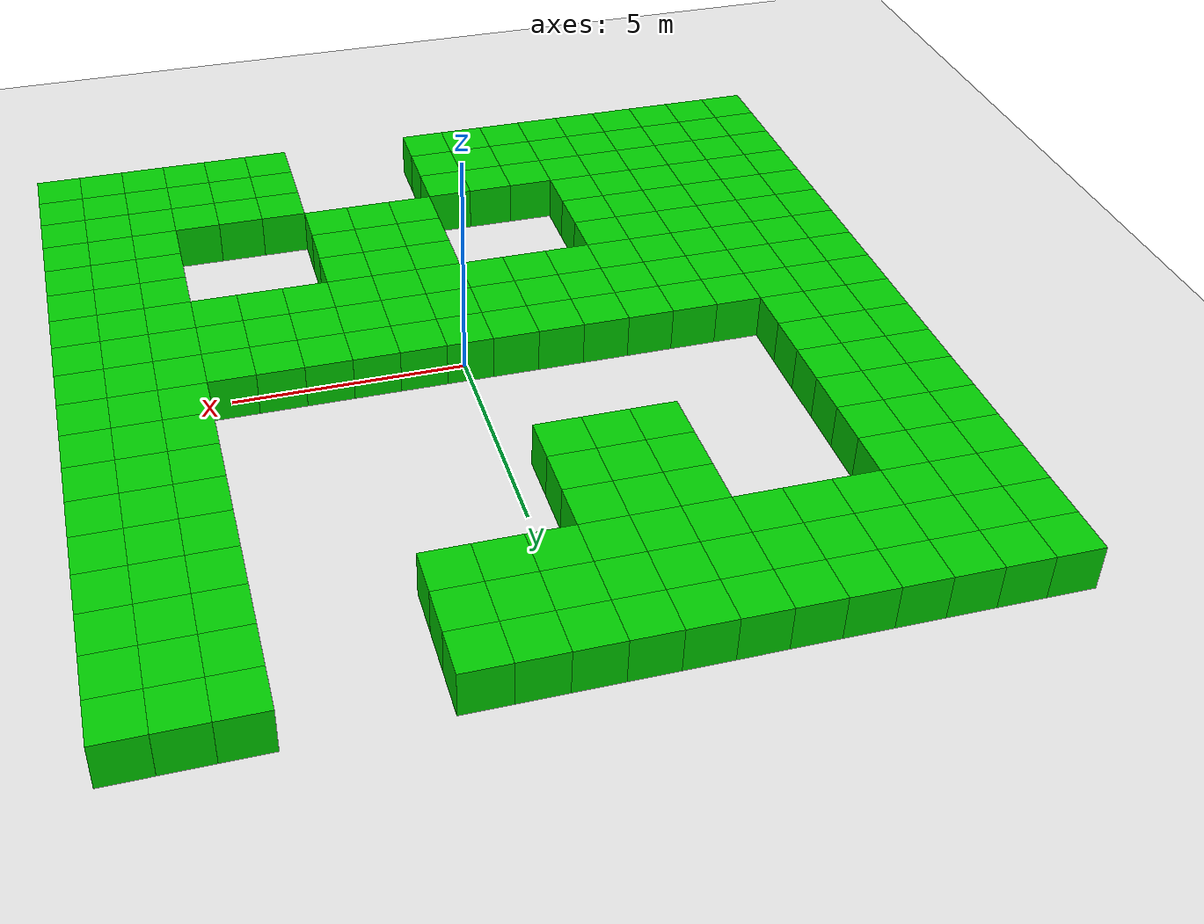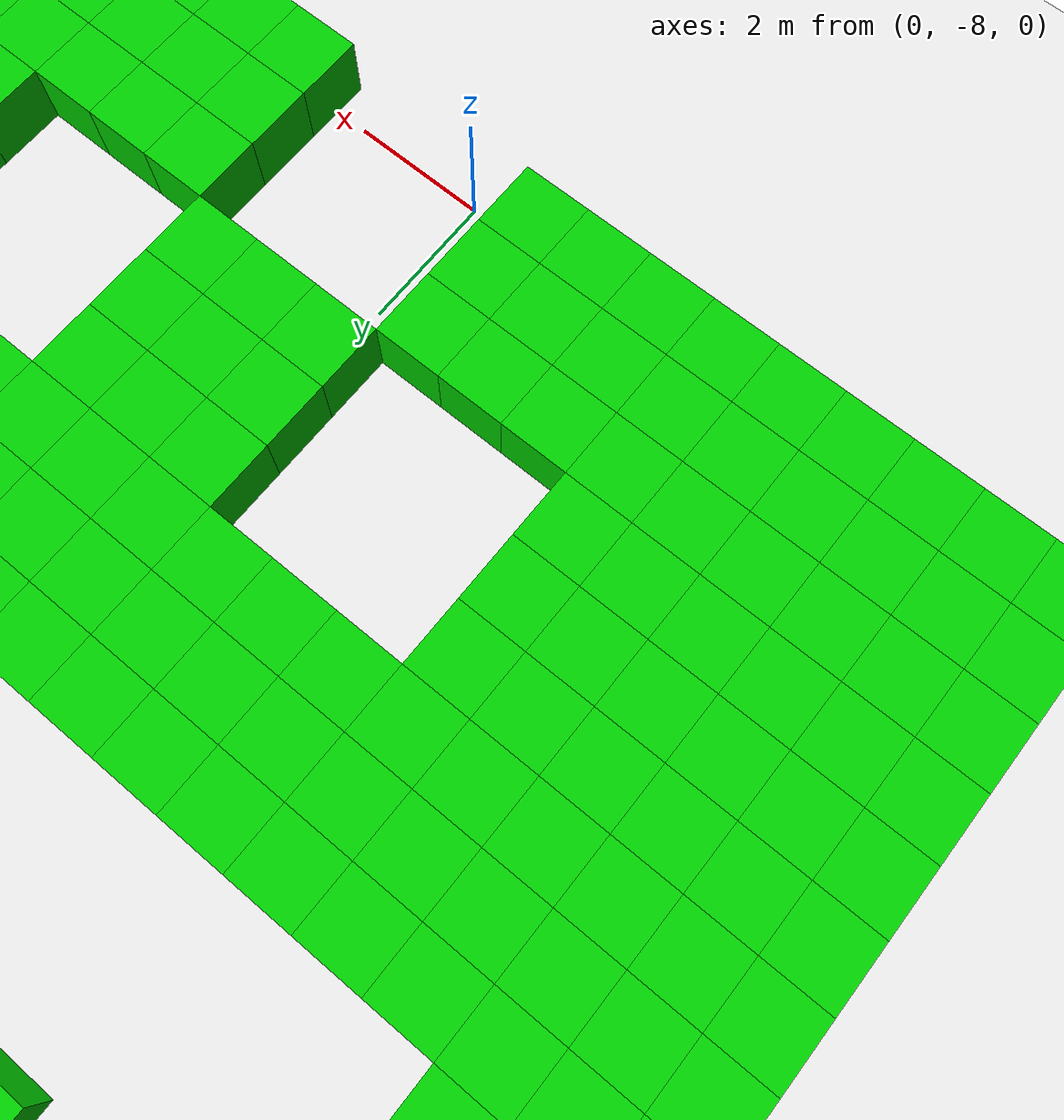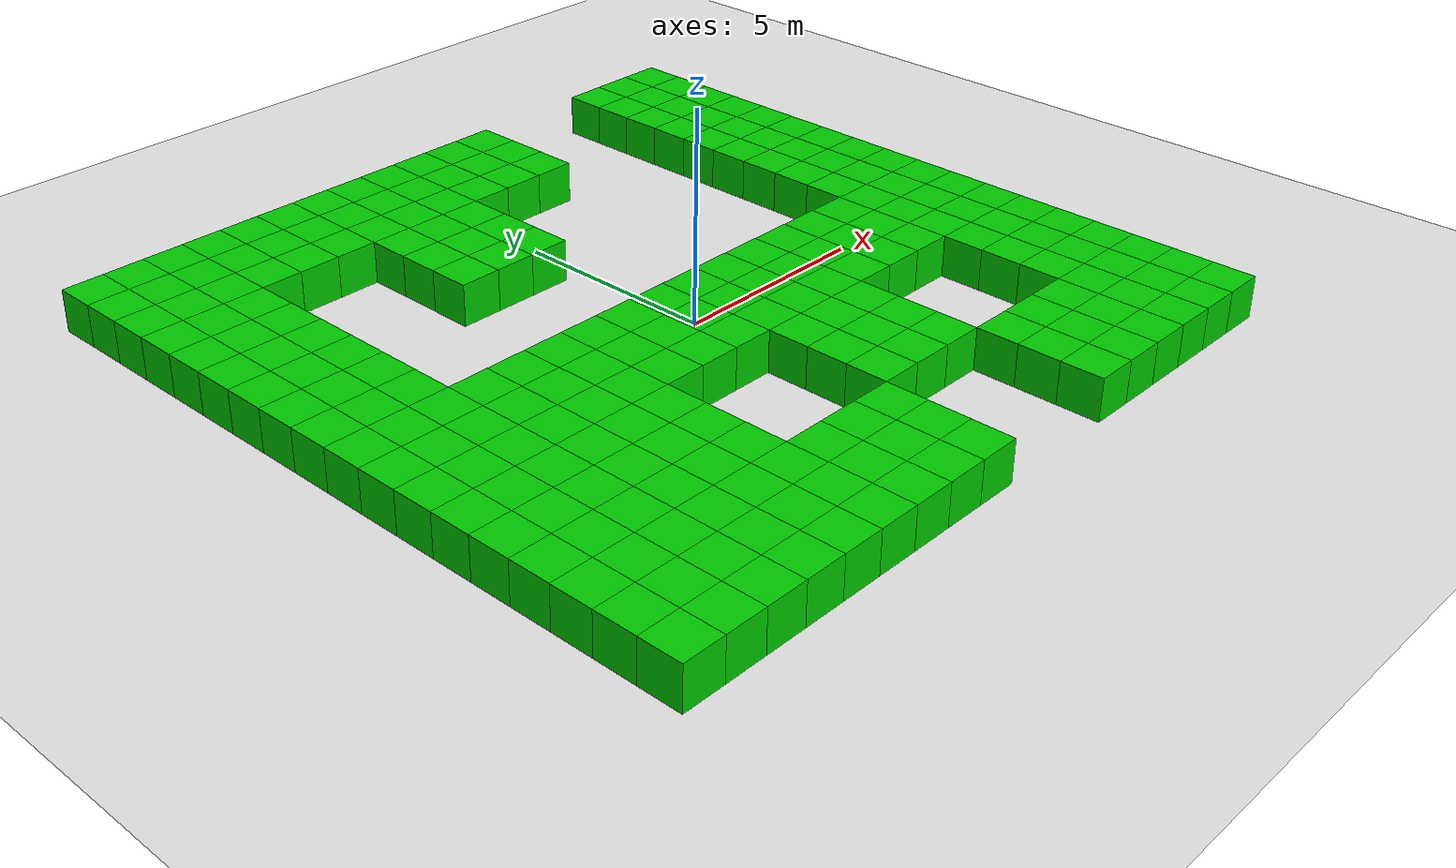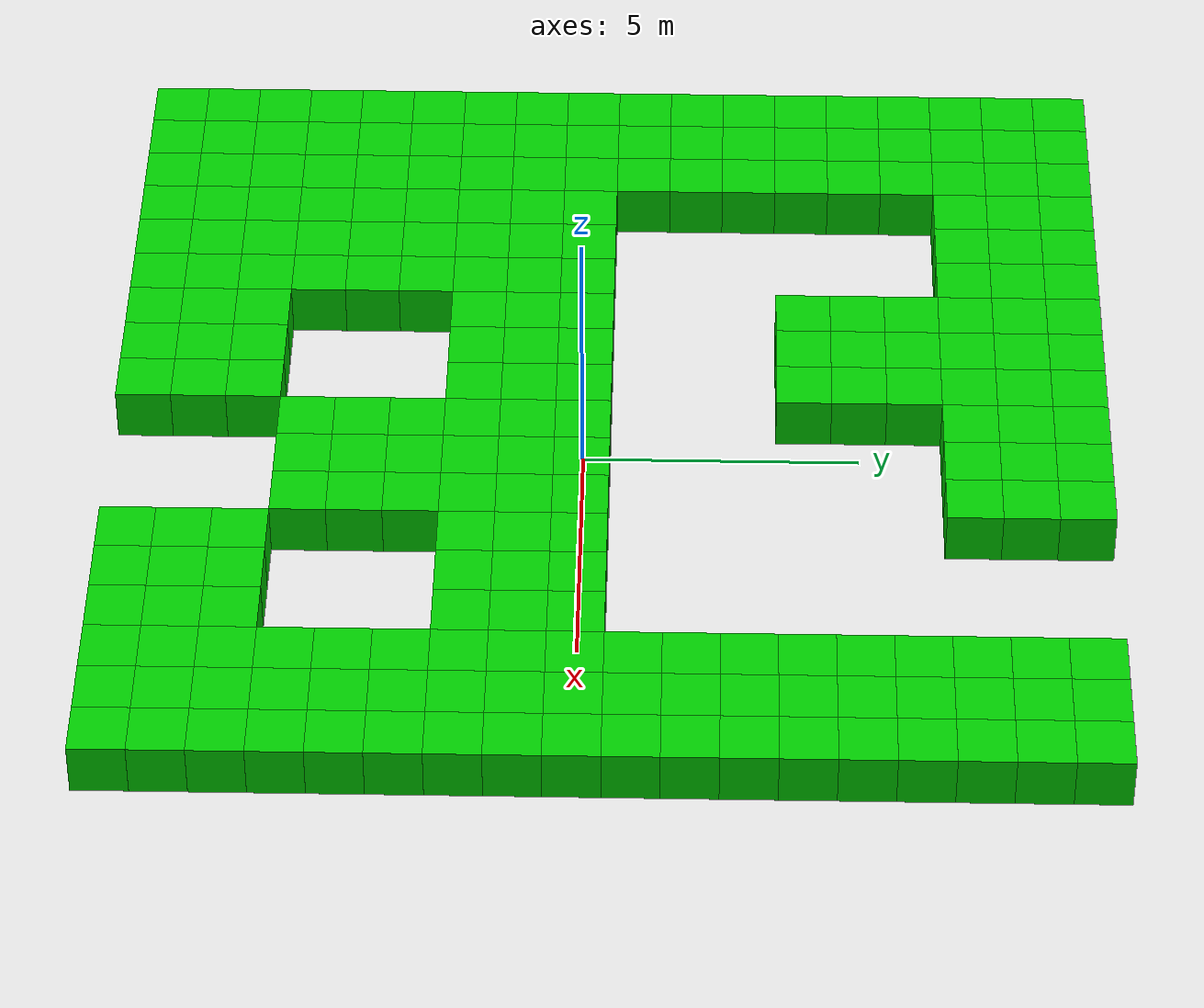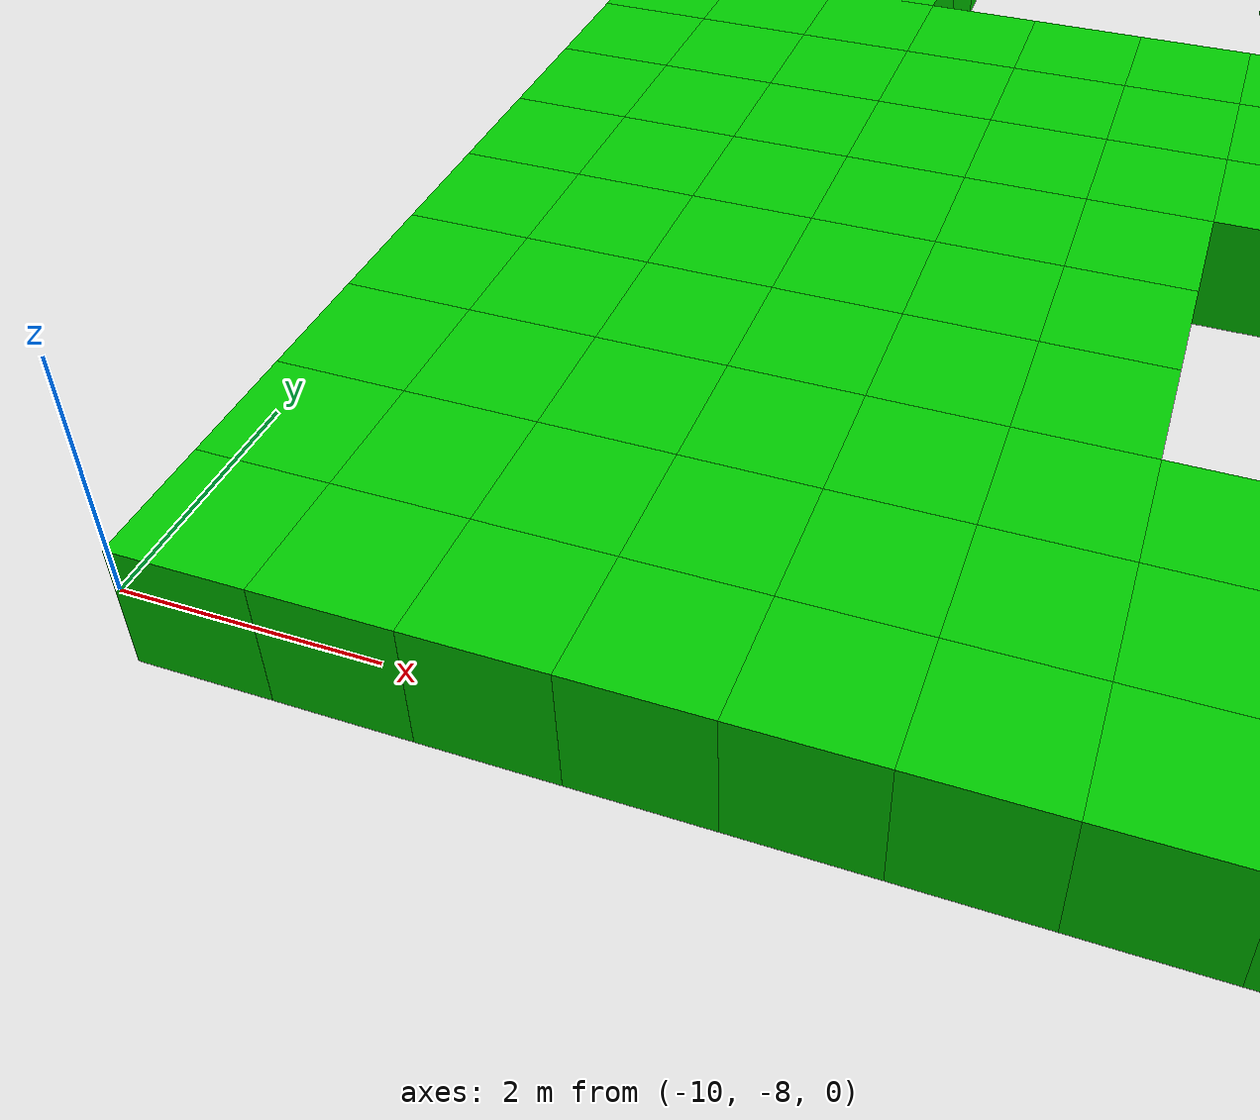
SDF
<?xml version="1.0" ?>
<sdf version="1.6">
  <world name="generated_maze">
    <light type="directional" name="sun">
      <cast_shadows>true</cast_shadows>
      <pose>0 0 10 0 0 0</pose>
      <diffuse>0.8 0.8 0.8 1</diffuse>
      <specular>0.2 0.2 0.2 1</specular>
      <attenuation>
        <range>1000</range>
        <constant>0.9</constant>
        <linear>0.01</linear>
        <quadratic>0.001</quadratic>
      </attenuation>
      <direction>-0.5 0.1 -0.9</direction>
    </light>

    <!-- Chão claro -->
    <model name="ground_plane">
      <static>true</static>
      <link name="link">
        <collision name="collision">
          <geometry><plane><normal>0 0 1</normal><size>100 100</size></plane></geometry>
        </collision>
        <visual name="visual">
          <geometry><plane><normal>0 0 1</normal><size>100 100</size></plane></geometry>
          <material>
            <ambient>0.9 0.9 0.9 1</ambient>
            <diffuse>0.9 0.9 0.9 1</diffuse>
            <specular>0.3 0.3 0.3 1</specular>
          </material>
        </visual>
      </link>
    </model>

    <model name="wall_0_0">
      <static>true</static>
      <pose>-9 9 0.5 0 0 0</pose>
      <link name="link">
        <collision name="collision">
          <geometry><box><size>1 1 1</size></box></geometry>
        </collision>
        <visual name="visual">
          <geometry><box><size>1 1 1</size></box></geometry>
          <material>
            <ambient>0.0 0.8 0.0 1</ambient>
            <diffuse>0.0 0.8 0.0 1</diffuse>
            <specular>0.1 0.1 0.1 1</specular>
          </material>
        </visual>
      </link>
    </model>

    <model name="wall_0_1">
      <static>true</static>
      <pose>-8 9 0.5 0 0 0</pose>
      <link name="link">
        <collision name="collision">
          <geometry><box><size>1 1 1</size></box></geometry>
        </collision>
        <visual name="visual">
          <geometry><box><size>1 1 1</size></box></geometry>
          <material>
            <ambient>0.0 0.8 0.0 1</ambient>
            <diffuse>0.0 0.8 0.0 1</diffuse>
            <specular>0.1 0.1 0.1 1</specular>
          </material>
        </visual>
      </link>
    </model>

    <model name="wall_0_2">
      <static>true</static>
      <pose>-7 9 0.5 0 0 0</pose>
      <link name="link">
        <collision name="collision">
          <geometry><box><size>1 1 1</size></box></geometry>
        </collision>
        <visual name="visual">
          <geometry><box><size>1 1 1</size></box></geometry>
          <material>
            <ambient>0.0 0.8 0.0 1</ambient>
            <diffuse>0.0 0.8 0.0 1</diffuse>
            <specular>0.1 0.1 0.1 1</specular>
          </material>
        </visual>
      </link>
    </model>

    <model name="wall_0_3">
      <static>true</static>
      <pose>-6 9 0.5 0 0 0</pose>
      <link name="link">
        <collision name="collision">
          <geometry><box><size>1 1 1</size></box></geometry>
        </collision>
        <visual name="visual">
          <geometry><box><size>1 1 1</size></box></geometry>
          <material>
            <ambient>0.0 0.8 0.0 1</ambient>
            <diffuse>0.0 0.8 0.0 1</diffuse>
            <specular>0.1 0.1 0.1 1</specular>
          </material>
        </visual>
      </link>
    </model>

    <model name="wall_0_4">
      <static>true</static>
      <pose>-5 9 0.5 0 0 0</pose>
      <link name="link">
        <collision name="collision">
          <geometry><box><size>1 1 1</size></box></geometry>
        </collision>
        <visual name="visual">
          <geometry><box><size>1 1 1</size></box></geometry>
          <material>
            <ambient>0.0 0.8 0.0 1</ambient>
            <diffuse>0.0 0.8 0.0 1</diffuse>
            <specular>0.1 0.1 0.1 1</specular>
          </material>
        </visual>
      </link>
    </model>

    <model name="wall_0_5">
      <static>true</static>
      <pose>-4 9 0.5 0 0 0</pose>
      <link name="link">
        <collision name="collision">
          <geometry><box><size>1 1 1</size></box></geometry>
        </collision>
        <visual name="visual">
          <geometry><box><size>1 1 1</size></box></geometry>
          <material>
            <ambient>0.0 0.8 0.0 1</ambient>
            <diffuse>0.0 0.8 0.0 1</diffuse>
            <specular>0.1 0.1 0.1 1</specular>
          </material>
        </visual>
      </link>
    </model>

    <model name="wall_0_6">
      <static>true</static>
      <pose>-3 9 0.5 0 0 0</pose>
      <link name="link">
        <collision name="collision">
          <geometry><box><size>1 1 1</size></box></geometry>
        </collision>
        <visual name="visual">
          <geometry><box><size>1 1 1</size></box></geometry>
          <material>
            <ambient>0.0 0.8 0.0 1</ambient>
            <diffuse>0.0 0.8 0.0 1</diffuse>
            <specular>0.1 0.1 0.1 1</specular>
          </material>
        </visual>
      </link>
    </model>

    <model name="wall_0_7">
      <static>true</static>
      <pose>-2 9 0.5 0 0 0</pose>
      <link name="link">
        <collision name="collision">
          <geometry><box><size>1 1 1</size></box></geometry>
        </collision>
        <visual name="visual">
          <geometry><box><size>1 1 1</size></box></geometry>
          <material>
            <ambient>0.0 0.8 0.0 1</ambient>
            <diffuse>0.0 0.8 0.0 1</diffuse>
            <specular>0.1 0.1 0.1 1</specular>
          </material>
        </visual>
      </link>
    </model>

    <model name="wall_0_8">
      <static>true</static>
      <pose>-1 9 0.5 0 0 0</pose>
      <link name="link">
        <collision name="collision">
          <geometry><box><size>1 1 1</size></box></geometry>
        </collision>
        <visual name="visual">
          <geometry><box><size>1 1 1</size></box></geometry>
          <material>
            <ambient>0.0 0.8 0.0 1</ambient>
            <diffuse>0.0 0.8 0.0 1</diffuse>
            <specular>0.1 0.1 0.1 1</specular>
          </material>
        </visual>
      </link>
    </model>

    <model name="wall_0_9">
      <static>true</static>
      <pose>0 9 0.5 0 0 0</pose>
      <link name="link">
        <collision name="collision">
          <geometry><box><size>1 1 1</size></box></geometry>
        </collision>
        <visual name="visual">
          <geometry><box><size>1 1 1</size></box></geometry>
          <material>
            <ambient>0.0 0.8 0.0 1</ambient>
            <diffuse>0.0 0.8 0.0 1</diffuse>
            <specular>0.1 0.1 0.1 1</specular>
          </material>
        </visual>
      </link>
    </model>

    <model name="wall_0_10">
      <static>true</static>
      <pose>1 9 0.5 0 0 0</pose>
      <link name="link">
        <collision name="collision">
          <geometry><box><size>1 1 1</size></box></geometry>
        </collision>
        <visual name="visual">
          <geometry><box><size>1 1 1</size></box></geometry>
          <material>
            <ambient>0.0 0.8 0.0 1</ambient>
            <diffuse>0.0 0.8 0.0 1</diffuse>
            <specular>0.1 0.1 0.1 1</specular>
          </material>
        </visual>
      </link>
    </model>

    <model name="wall_0_11">
      <static>true</static>
      <pose>2 9 0.5 0 0 0</pose>
      <link name="link">
        <collision name="collision">
          <geometry><box><size>1 1 1</size></box></geometry>
        </collision>
        <visual name="visual">
          <geometry><box><size>1 1 1</size></box></geometry>
          <material>
            <ambient>0.0 0.8 0.0 1</ambient>
            <diffuse>0.0 0.8 0.0 1</diffuse>
            <specular>0.1 0.1 0.1 1</specular>
          </material>
        </visual>
      </link>
    </model>

    <model name="wall_0_15">
      <static>true</static>
      <pose>6 9 0.5 0 0 0</pose>
      <link name="link">
        <collision name="collision">
          <geometry><box><size>1 1 1</size></box></geometry>
        </collision>
        <visual name="visual">
          <geometry><box><size>1 1 1</size></box></geometry>
          <material>
            <ambient>0.0 0.8 0.0 1</ambient>
            <diffuse>0.0 0.8 0.0 1</diffuse>
            <specular>0.1 0.1 0.1 1</specular>
          </material>
        </visual>
      </link>
    </model>

    <model name="wall_0_16">
      <static>true</static>
      <pose>7 9 0.5 0 0 0</pose>
      <link name="link">
        <collision name="collision">
          <geometry><box><size>1 1 1</size></box></geometry>
        </collision>
        <visual name="visual">
          <geometry><box><size>1 1 1</size></box></geometry>
          <material>
            <ambient>0.0 0.8 0.0 1</ambient>
            <diffuse>0.0 0.8 0.0 1</diffuse>
            <specular>0.1 0.1 0.1 1</specular>
          </material>
        </visual>
      </link>
    </model>

    <model name="wall_0_17">
      <static>true</static>
      <pose>8 9 0.5 0 0 0</pose>
      <link name="link">
        <collision name="collision">
          <geometry><box><size>1 1 1</size></box></geometry>
        </collision>
        <visual name="visual">
          <geometry><box><size>1 1 1</size></box></geometry>
          <material>
            <ambient>0.0 0.8 0.0 1</ambient>
            <diffuse>0.0 0.8 0.0 1</diffuse>
            <specular>0.1 0.1 0.1 1</specular>
          </material>
        </visual>
      </link>
    </model>

    <model name="wall_1_0">
      <static>true</static>
      <pose>-9 8 0.5 0 0 0</pose>
      <link name="link">
        <collision name="collision">
          <geometry><box><size>1 1 1</size></box></geometry>
        </collision>
        <visual name="visual">
          <geometry><box><size>1 1 1</size></box></geometry>
          <material>
            <ambient>0.0 0.8 0.0 1</ambient>
            <diffuse>0.0 0.8 0.0 1</diffuse>
            <specular>0.1 0.1 0.1 1</specular>
          </material>
        </visual>
      </link>
    </model>

    <model name="wall_1_1">
      <static>true</static>
      <pose>-8 8 0.5 0 0 0</pose>
      <link name="link">
        <collision name="collision">
          <geometry><box><size>1 1 1</size></box></geometry>
        </collision>
        <visual name="visual">
          <geometry><box><size>1 1 1</size></box></geometry>
          <material>
            <ambient>0.0 0.8 0.0 1</ambient>
            <diffuse>0.0 0.8 0.0 1</diffuse>
            <specular>0.1 0.1 0.1 1</specular>
          </material>
        </visual>
      </link>
    </model>

    <model name="wall_1_2">
      <static>true</static>
      <pose>-7 8 0.5 0 0 0</pose>
      <link name="link">
        <collision name="collision">
          <geometry><box><size>1 1 1</size></box></geometry>
        </collision>
        <visual name="visual">
          <geometry><box><size>1 1 1</size></box></geometry>
          <material>
            <ambient>0.0 0.8 0.0 1</ambient>
            <diffuse>0.0 0.8 0.0 1</diffuse>
            <specular>0.1 0.1 0.1 1</specular>
          </material>
        </visual>
      </link>
    </model>

    <model name="wall_1_3">
      <static>true</static>
      <pose>-6 8 0.5 0 0 0</pose>
      <link name="link">
        <collision name="collision">
          <geometry><box><size>1 1 1</size></box></geometry>
        </collision>
        <visual name="visual">
          <geometry><box><size>1 1 1</size></box></geometry>
          <material>
            <ambient>0.0 0.8 0.0 1</ambient>
            <diffuse>0.0 0.8 0.0 1</diffuse>
            <specular>0.1 0.1 0.1 1</specular>
          </material>
        </visual>
      </link>
    </model>

    <model name="wall_1_4">
      <static>true</static>
      <pose>-5 8 0.5 0 0 0</pose>
      <link name="link">
        <collision name="collision">
          <geometry><box><size>1 1 1</size></box></geometry>
        </collision>
        <visual name="visual">
          <geometry><box><size>1 1 1</size></box></geometry>
          <material>
            <ambient>0.0 0.8 0.0 1</ambient>
            <diffuse>0.0 0.8 0.0 1</diffuse>
            <specular>0.1 0.1 0.1 1</specular>
          </material>
        </visual>
      </link>
    </model>

    <model name="wall_1_5">
      <static>true</static>
      <pose>-4 8 0.5 0 0 0</pose>
      <link name="link">
        <collision name="collision">
          <geometry><box><size>1 1 1</size></box></geometry>
        </collision>
        <visual name="visual">
          <geometry><box><size>1 1 1</size></box></geometry>
          <material>
            <ambient>0.0 0.8 0.0 1</ambient>
            <diffuse>0.0 0.8 0.0 1</diffuse>
            <specular>0.1 0.1 0.1 1</specular>
          </material>
        </visual>
      </link>
    </model>

    <model name="wall_1_6">
      <static>true</static>
      <pose>-3 8 0.5 0 0 0</pose>
      <link name="link">
        <collision name="collision">
          <geometry><box><size>1 1 1</size></box></geometry>
        </collision>
        <visual name="visual">
          <geometry><box><size>1 1 1</size></box></geometry>
          <material>
            <ambient>0.0 0.8 0.0 1</ambient>
            <diffuse>0.0 0.8 0.0 1</diffuse>
            <specular>0.1 0.1 0.1 1</specular>
          </material>
        </visual>
      </link>
    </model>

    <model name="wall_1_7">
      <static>true</static>
      <pose>-2 8 0.5 0 0 0</pose>
      <link name="link">
        <collision name="collision">
          <geometry><box><size>1 1 1</size></box></geometry>
        </collision>
        <visual name="visual">
          <geometry><box><size>1 1 1</size></box></geometry>
          <material>
            <ambient>0.0 0.8 0.0 1</ambient>
            <diffuse>0.0 0.8 0.0 1</diffuse>
            <specular>0.1 0.1 0.1 1</specular>
          </material>
        </visual>
      </link>
    </model>

    <model name="wall_1_8">
      <static>true</static>
      <pose>-1 8 0.5 0 0 0</pose>
      <link name="link">
        <collision name="collision">
          <geometry><box><size>1 1 1</size></box></geometry>
        </collision>
        <visual name="visual">
          <geometry><box><size>1 1 1</size></box></geometry>
          <material>
            <ambient>0.0 0.8 0.0 1</ambient>
            <diffuse>0.0 0.8 0.0 1</diffuse>
            <specular>0.1 0.1 0.1 1</specular>
          </material>
        </visual>
      </link>
    </model>

    <model name="wall_1_9">
      <static>true</static>
      <pose>0 8 0.5 0 0 0</pose>
      <link name="link">
        <collision name="collision">
          <geometry><box><size>1 1 1</size></box></geometry>
        </collision>
        <visual name="visual">
          <geometry><box><size>1 1 1</size></box></geometry>
          <material>
            <ambient>0.0 0.8 0.0 1</ambient>
            <diffuse>0.0 0.8 0.0 1</diffuse>
            <specular>0.1 0.1 0.1 1</specular>
          </material>
        </visual>
      </link>
    </model>

    <model name="wall_1_10">
      <static>true</static>
      <pose>1 8 0.5 0 0 0</pose>
      <link name="link">
        <collision name="collision">
          <geometry><box><size>1 1 1</size></box></geometry>
        </collision>
        <visual name="visual">
          <geometry><box><size>1 1 1</size></box></geometry>
          <material>
            <ambient>0.0 0.8 0.0 1</ambient>
            <diffuse>0.0 0.8 0.0 1</diffuse>
            <specular>0.1 0.1 0.1 1</specular>
          </material>
        </visual>
      </link>
    </model>

    <model name="wall_1_11">
      <static>true</static>
      <pose>2 8 0.5 0 0 0</pose>
      <link name="link">
        <collision name="collision">
          <geometry><box><size>1 1 1</size></box></geometry>
        </collision>
        <visual name="visual">
          <geometry><box><size>1 1 1</size></box></geometry>
          <material>
            <ambient>0.0 0.8 0.0 1</ambient>
            <diffuse>0.0 0.8 0.0 1</diffuse>
            <specular>0.1 0.1 0.1 1</specular>
          </material>
        </visual>
      </link>
    </model>

    <model name="wall_1_15">
      <static>true</static>
      <pose>6 8 0.5 0 0 0</pose>
      <link name="link">
        <collision name="collision">
          <geometry><box><size>1 1 1</size></box></geometry>
        </collision>
        <visual name="visual">
          <geometry><box><size>1 1 1</size></box></geometry>
          <material>
            <ambient>0.0 0.8 0.0 1</ambient>
            <diffuse>0.0 0.8 0.0 1</diffuse>
            <specular>0.1 0.1 0.1 1</specular>
          </material>
        </visual>
      </link>
    </model>

    <model name="wall_1_16">
      <static>true</static>
      <pose>7 8 0.5 0 0 0</pose>
      <link name="link">
        <collision name="collision">
          <geometry><box><size>1 1 1</size></box></geometry>
        </collision>
        <visual name="visual">
          <geometry><box><size>1 1 1</size></box></geometry>
          <material>
            <ambient>0.0 0.8 0.0 1</ambient>
            <diffuse>0.0 0.8 0.0 1</diffuse>
            <specular>0.1 0.1 0.1 1</specular>
          </material>
        </visual>
      </link>
    </model>

    <model name="wall_1_17">
      <static>true</static>
      <pose>8 8 0.5 0 0 0</pose>
      <link name="link">
        <collision name="collision">
          <geometry><box><size>1 1 1</size></box></geometry>
        </collision>
        <visual name="visual">
          <geometry><box><size>1 1 1</size></box></geometry>
          <material>
            <ambient>0.0 0.8 0.0 1</ambient>
            <diffuse>0.0 0.8 0.0 1</diffuse>
            <specular>0.1 0.1 0.1 1</specular>
          </material>
        </visual>
      </link>
    </model>

    <model name="wall_2_0">
      <static>true</static>
      <pose>-9 7 0.5 0 0 0</pose>
      <link name="link">
        <collision name="collision">
          <geometry><box><size>1 1 1</size></box></geometry>
        </collision>
        <visual name="visual">
          <geometry><box><size>1 1 1</size></box></geometry>
          <material>
            <ambient>0.0 0.8 0.0 1</ambient>
            <diffuse>0.0 0.8 0.0 1</diffuse>
            <specular>0.1 0.1 0.1 1</specular>
          </material>
        </visual>
      </link>
    </model>

    <model name="wall_2_1">
      <static>true</static>
      <pose>-8 7 0.5 0 0 0</pose>
      <link name="link">
        <collision name="collision">
          <geometry><box><size>1 1 1</size></box></geometry>
        </collision>
        <visual name="visual">
          <geometry><box><size>1 1 1</size></box></geometry>
          <material>
            <ambient>0.0 0.8 0.0 1</ambient>
            <diffuse>0.0 0.8 0.0 1</diffuse>
            <specular>0.1 0.1 0.1 1</specular>
          </material>
        </visual>
      </link>
    </model>

    <model name="wall_2_2">
      <static>true</static>
      <pose>-7 7 0.5 0 0 0</pose>
      <link name="link">
        <collision name="collision">
          <geometry><box><size>1 1 1</size></box></geometry>
        </collision>
        <visual name="visual">
          <geometry><box><size>1 1 1</size></box></geometry>
          <material>
            <ambient>0.0 0.8 0.0 1</ambient>
            <diffuse>0.0 0.8 0.0 1</diffuse>
            <specular>0.1 0.1 0.1 1</specular>
          </material>
        </visual>
      </link>
    </model>

    <model name="wall_2_3">
      <static>true</static>
      <pose>-6 7 0.5 0 0 0</pose>
      <link name="link">
        <collision name="collision">
          <geometry><box><size>1 1 1</size></box></geometry>
        </collision>
        <visual name="visual">
          <geometry><box><size>1 1 1</size></box></geometry>
          <material>
            <ambient>0.0 0.8 0.0 1</ambient>
            <diffuse>0.0 0.8 0.0 1</diffuse>
            <specular>0.1 0.1 0.1 1</specular>
          </material>
        </visual>
      </link>
    </model>

    <model name="wall_2_4">
      <static>true</static>
      <pose>-5 7 0.5 0 0 0</pose>
      <link name="link">
        <collision name="collision">
          <geometry><box><size>1 1 1</size></box></geometry>
        </collision>
        <visual name="visual">
          <geometry><box><size>1 1 1</size></box></geometry>
          <material>
            <ambient>0.0 0.8 0.0 1</ambient>
            <diffuse>0.0 0.8 0.0 1</diffuse>
            <specular>0.1 0.1 0.1 1</specular>
          </material>
        </visual>
      </link>
    </model>

    <model name="wall_2_5">
      <static>true</static>
      <pose>-4 7 0.5 0 0 0</pose>
      <link name="link">
        <collision name="collision">
          <geometry><box><size>1 1 1</size></box></geometry>
        </collision>
        <visual name="visual">
          <geometry><box><size>1 1 1</size></box></geometry>
          <material>
            <ambient>0.0 0.8 0.0 1</ambient>
            <diffuse>0.0 0.8 0.0 1</diffuse>
            <specular>0.1 0.1 0.1 1</specular>
          </material>
        </visual>
      </link>
    </model>

    <model name="wall_2_6">
      <static>true</static>
      <pose>-3 7 0.5 0 0 0</pose>
      <link name="link">
        <collision name="collision">
          <geometry><box><size>1 1 1</size></box></geometry>
        </collision>
        <visual name="visual">
          <geometry><box><size>1 1 1</size></box></geometry>
          <material>
            <ambient>0.0 0.8 0.0 1</ambient>
            <diffuse>0.0 0.8 0.0 1</diffuse>
            <specular>0.1 0.1 0.1 1</specular>
          </material>
        </visual>
      </link>
    </model>

    <model name="wall_2_7">
      <static>true</static>
      <pose>-2 7 0.5 0 0 0</pose>
      <link name="link">
        <collision name="collision">
          <geometry><box><size>1 1 1</size></box></geometry>
        </collision>
        <visual name="visual">
          <geometry><box><size>1 1 1</size></box></geometry>
          <material>
            <ambient>0.0 0.8 0.0 1</ambient>
            <diffuse>0.0 0.8 0.0 1</diffuse>
            <specular>0.1 0.1 0.1 1</specular>
          </material>
        </visual>
      </link>
    </model>

    <model name="wall_2_8">
      <static>true</static>
      <pose>-1 7 0.5 0 0 0</pose>
      <link name="link">
        <collision name="collision">
          <geometry><box><size>1 1 1</size></box></geometry>
        </collision>
        <visual name="visual">
          <geometry><box><size>1 1 1</size></box></geometry>
          <material>
            <ambient>0.0 0.8 0.0 1</ambient>
            <diffuse>0.0 0.8 0.0 1</diffuse>
            <specular>0.1 0.1 0.1 1</specular>
          </material>
        </visual>
      </link>
    </model>

    <model name="wall_2_9">
      <static>true</static>
      <pose>0 7 0.5 0 0 0</pose>
      <link name="link">
        <collision name="collision">
          <geometry><box><size>1 1 1</size></box></geometry>
        </collision>
        <visual name="visual">
          <geometry><box><size>1 1 1</size></box></geometry>
          <material>
            <ambient>0.0 0.8 0.0 1</ambient>
            <diffuse>0.0 0.8 0.0 1</diffuse>
            <specular>0.1 0.1 0.1 1</specular>
          </material>
        </visual>
      </link>
    </model>

    <model name="wall_2_10">
      <static>true</static>
      <pose>1 7 0.5 0 0 0</pose>
      <link name="link">
        <collision name="collision">
          <geometry><box><size>1 1 1</size></box></geometry>
        </collision>
        <visual name="visual">
          <geometry><box><size>1 1 1</size></box></geometry>
          <material>
            <ambient>0.0 0.8 0.0 1</ambient>
            <diffuse>0.0 0.8 0.0 1</diffuse>
            <specular>0.1 0.1 0.1 1</specular>
          </material>
        </visual>
      </link>
    </model>

    <model name="wall_2_11">
      <static>true</static>
      <pose>2 7 0.5 0 0 0</pose>
      <link name="link">
        <collision name="collision">
          <geometry><box><size>1 1 1</size></box></geometry>
        </collision>
        <visual name="visual">
          <geometry><box><size>1 1 1</size></box></geometry>
          <material>
            <ambient>0.0 0.8 0.0 1</ambient>
            <diffuse>0.0 0.8 0.0 1</diffuse>
            <specular>0.1 0.1 0.1 1</specular>
          </material>
        </visual>
      </link>
    </model>

    <model name="wall_2_15">
      <static>true</static>
      <pose>6 7 0.5 0 0 0</pose>
      <link name="link">
        <collision name="collision">
          <geometry><box><size>1 1 1</size></box></geometry>
        </collision>
        <visual name="visual">
          <geometry><box><size>1 1 1</size></box></geometry>
          <material>
            <ambient>0.0 0.8 0.0 1</ambient>
            <diffuse>0.0 0.8 0.0 1</diffuse>
            <specular>0.1 0.1 0.1 1</specular>
          </material>
        </visual>
      </link>
    </model>

    <model name="wall_2_16">
      <static>true</static>
      <pose>7 7 0.5 0 0 0</pose>
      <link name="link">
        <collision name="collision">
          <geometry><box><size>1 1 1</size></box></geometry>
        </collision>
        <visual name="visual">
          <geometry><box><size>1 1 1</size></box></geometry>
          <material>
            <ambient>0.0 0.8 0.0 1</ambient>
            <diffuse>0.0 0.8 0.0 1</diffuse>
            <specular>0.1 0.1 0.1 1</specular>
          </material>
        </visual>
      </link>
    </model>

    <model name="wall_2_17">
      <static>true</static>
      <pose>8 7 0.5 0 0 0</pose>
      <link name="link">
        <collision name="collision">
          <geometry><box><size>1 1 1</size></box></geometry>
        </collision>
        <visual name="visual">
          <geometry><box><size>1 1 1</size></box></geometry>
          <material>
            <ambient>0.0 0.8 0.0 1</ambient>
            <diffuse>0.0 0.8 0.0 1</diffuse>
            <specular>0.1 0.1 0.1 1</specular>
          </material>
        </visual>
      </link>
    </model>

    <model name="wall_3_0">
      <static>true</static>
      <pose>-9 6 0.5 0 0 0</pose>
      <link name="link">
        <collision name="collision">
          <geometry><box><size>1 1 1</size></box></geometry>
        </collision>
        <visual name="visual">
          <geometry><box><size>1 1 1</size></box></geometry>
          <material>
            <ambient>0.0 0.8 0.0 1</ambient>
            <diffuse>0.0 0.8 0.0 1</diffuse>
            <specular>0.1 0.1 0.1 1</specular>
          </material>
        </visual>
      </link>
    </model>

    <model name="wall_3_1">
      <static>true</static>
      <pose>-8 6 0.5 0 0 0</pose>
      <link name="link">
        <collision name="collision">
          <geometry><box><size>1 1 1</size></box></geometry>
        </collision>
        <visual name="visual">
          <geometry><box><size>1 1 1</size></box></geometry>
          <material>
            <ambient>0.0 0.8 0.0 1</ambient>
            <diffuse>0.0 0.8 0.0 1</diffuse>
            <specular>0.1 0.1 0.1 1</specular>
          </material>
        </visual>
      </link>
    </model>

    <model name="wall_3_2">
      <static>true</static>
      <pose>-7 6 0.5 0 0 0</pose>
      <link name="link">
        <collision name="collision">
          <geometry><box><size>1 1 1</size></box></geometry>
        </collision>
        <visual name="visual">
          <geometry><box><size>1 1 1</size></box></geometry>
          <material>
            <ambient>0.0 0.8 0.0 1</ambient>
            <diffuse>0.0 0.8 0.0 1</diffuse>
            <specular>0.1 0.1 0.1 1</specular>
          </material>
        </visual>
      </link>
    </model>

    <model name="wall_3_6">
      <static>true</static>
      <pose>-3 6 0.5 0 0 0</pose>
      <link name="link">
        <collision name="collision">
          <geometry><box><size>1 1 1</size></box></geometry>
        </collision>
        <visual name="visual">
          <geometry><box><size>1 1 1</size></box></geometry>
          <material>
            <ambient>0.0 0.8 0.0 1</ambient>
            <diffuse>0.0 0.8 0.0 1</diffuse>
            <specular>0.1 0.1 0.1 1</specular>
          </material>
        </visual>
      </link>
    </model>

    <model name="wall_3_7">
      <static>true</static>
      <pose>-2 6 0.5 0 0 0</pose>
      <link name="link">
        <collision name="collision">
          <geometry><box><size>1 1 1</size></box></geometry>
        </collision>
        <visual name="visual">
          <geometry><box><size>1 1 1</size></box></geometry>
          <material>
            <ambient>0.0 0.8 0.0 1</ambient>
            <diffuse>0.0 0.8 0.0 1</diffuse>
            <specular>0.1 0.1 0.1 1</specular>
          </material>
        </visual>
      </link>
    </model>

    <model name="wall_3_8">
      <static>true</static>
      <pose>-1 6 0.5 0 0 0</pose>
      <link name="link">
        <collision name="collision">
          <geometry><box><size>1 1 1</size></box></geometry>
        </collision>
        <visual name="visual">
          <geometry><box><size>1 1 1</size></box></geometry>
          <material>
            <ambient>0.0 0.8 0.0 1</ambient>
            <diffuse>0.0 0.8 0.0 1</diffuse>
            <specular>0.1 0.1 0.1 1</specular>
          </material>
        </visual>
      </link>
    </model>

    <model name="wall_3_15">
      <static>true</static>
      <pose>6 6 0.5 0 0 0</pose>
      <link name="link">
        <collision name="collision">
          <geometry><box><size>1 1 1</size></box></geometry>
        </collision>
        <visual name="visual">
          <geometry><box><size>1 1 1</size></box></geometry>
          <material>
            <ambient>0.0 0.8 0.0 1</ambient>
            <diffuse>0.0 0.8 0.0 1</diffuse>
            <specular>0.1 0.1 0.1 1</specular>
          </material>
        </visual>
      </link>
    </model>

    <model name="wall_3_16">
      <static>true</static>
      <pose>7 6 0.5 0 0 0</pose>
      <link name="link">
        <collision name="collision">
          <geometry><box><size>1 1 1</size></box></geometry>
        </collision>
        <visual name="visual">
          <geometry><box><size>1 1 1</size></box></geometry>
          <material>
            <ambient>0.0 0.8 0.0 1</ambient>
            <diffuse>0.0 0.8 0.0 1</diffuse>
            <specular>0.1 0.1 0.1 1</specular>
          </material>
        </visual>
      </link>
    </model>

    <model name="wall_3_17">
      <static>true</static>
      <pose>8 6 0.5 0 0 0</pose>
      <link name="link">
        <collision name="collision">
          <geometry><box><size>1 1 1</size></box></geometry>
        </collision>
        <visual name="visual">
          <geometry><box><size>1 1 1</size></box></geometry>
          <material>
            <ambient>0.0 0.8 0.0 1</ambient>
            <diffuse>0.0 0.8 0.0 1</diffuse>
            <specular>0.1 0.1 0.1 1</specular>
          </material>
        </visual>
      </link>
    </model>

    <model name="wall_4_0">
      <static>true</static>
      <pose>-9 5 0.5 0 0 0</pose>
      <link name="link">
        <collision name="collision">
          <geometry><box><size>1 1 1</size></box></geometry>
        </collision>
        <visual name="visual">
          <geometry><box><size>1 1 1</size></box></geometry>
          <material>
            <ambient>0.0 0.8 0.0 1</ambient>
            <diffuse>0.0 0.8 0.0 1</diffuse>
            <specular>0.1 0.1 0.1 1</specular>
          </material>
        </visual>
      </link>
    </model>

    <model name="wall_4_1">
      <static>true</static>
      <pose>-8 5 0.5 0 0 0</pose>
      <link name="link">
        <collision name="collision">
          <geometry><box><size>1 1 1</size></box></geometry>
        </collision>
        <visual name="visual">
          <geometry><box><size>1 1 1</size></box></geometry>
          <material>
            <ambient>0.0 0.8 0.0 1</ambient>
            <diffuse>0.0 0.8 0.0 1</diffuse>
            <specular>0.1 0.1 0.1 1</specular>
          </material>
        </visual>
      </link>
    </model>

    <model name="wall_4_2">
      <static>true</static>
      <pose>-7 5 0.5 0 0 0</pose>
      <link name="link">
        <collision name="collision">
          <geometry><box><size>1 1 1</size></box></geometry>
        </collision>
        <visual name="visual">
          <geometry><box><size>1 1 1</size></box></geometry>
          <material>
            <ambient>0.0 0.8 0.0 1</ambient>
            <diffuse>0.0 0.8 0.0 1</diffuse>
            <specular>0.1 0.1 0.1 1</specular>
          </material>
        </visual>
      </link>
    </model>

    <model name="wall_4_6">
      <static>true</static>
      <pose>-3 5 0.5 0 0 0</pose>
      <link name="link">
        <collision name="collision">
          <geometry><box><size>1 1 1</size></box></geometry>
        </collision>
        <visual name="visual">
          <geometry><box><size>1 1 1</size></box></geometry>
          <material>
            <ambient>0.0 0.8 0.0 1</ambient>
            <diffuse>0.0 0.8 0.0 1</diffuse>
            <specular>0.1 0.1 0.1 1</specular>
          </material>
        </visual>
      </link>
    </model>

    <model name="wall_4_7">
      <static>true</static>
      <pose>-2 5 0.5 0 0 0</pose>
      <link name="link">
        <collision name="collision">
          <geometry><box><size>1 1 1</size></box></geometry>
        </collision>
        <visual name="visual">
          <geometry><box><size>1 1 1</size></box></geometry>
          <material>
            <ambient>0.0 0.8 0.0 1</ambient>
            <diffuse>0.0 0.8 0.0 1</diffuse>
            <specular>0.1 0.1 0.1 1</specular>
          </material>
        </visual>
      </link>
    </model>

    <model name="wall_4_8">
      <static>true</static>
      <pose>-1 5 0.5 0 0 0</pose>
      <link name="link">
        <collision name="collision">
          <geometry><box><size>1 1 1</size></box></geometry>
        </collision>
        <visual name="visual">
          <geometry><box><size>1 1 1</size></box></geometry>
          <material>
            <ambient>0.0 0.8 0.0 1</ambient>
            <diffuse>0.0 0.8 0.0 1</diffuse>
            <specular>0.1 0.1 0.1 1</specular>
          </material>
        </visual>
      </link>
    </model>

    <model name="wall_4_15">
      <static>true</static>
      <pose>6 5 0.5 0 0 0</pose>
      <link name="link">
        <collision name="collision">
          <geometry><box><size>1 1 1</size></box></geometry>
        </collision>
        <visual name="visual">
          <geometry><box><size>1 1 1</size></box></geometry>
          <material>
            <ambient>0.0 0.8 0.0 1</ambient>
            <diffuse>0.0 0.8 0.0 1</diffuse>
            <specular>0.1 0.1 0.1 1</specular>
          </material>
        </visual>
      </link>
    </model>

    <model name="wall_4_16">
      <static>true</static>
      <pose>7 5 0.5 0 0 0</pose>
      <link name="link">
        <collision name="collision">
          <geometry><box><size>1 1 1</size></box></geometry>
        </collision>
        <visual name="visual">
          <geometry><box><size>1 1 1</size></box></geometry>
          <material>
            <ambient>0.0 0.8 0.0 1</ambient>
            <diffuse>0.0 0.8 0.0 1</diffuse>
            <specular>0.1 0.1 0.1 1</specular>
          </material>
        </visual>
      </link>
    </model>

    <model name="wall_4_17">
      <static>true</static>
      <pose>8 5 0.5 0 0 0</pose>
      <link name="link">
        <collision name="collision">
          <geometry><box><size>1 1 1</size></box></geometry>
        </collision>
        <visual name="visual">
          <geometry><box><size>1 1 1</size></box></geometry>
          <material>
            <ambient>0.0 0.8 0.0 1</ambient>
            <diffuse>0.0 0.8 0.0 1</diffuse>
            <specular>0.1 0.1 0.1 1</specular>
          </material>
        </visual>
      </link>
    </model>

    <model name="wall_5_0">
      <static>true</static>
      <pose>-9 4 0.5 0 0 0</pose>
      <link name="link">
        <collision name="collision">
          <geometry><box><size>1 1 1</size></box></geometry>
        </collision>
        <visual name="visual">
          <geometry><box><size>1 1 1</size></box></geometry>
          <material>
            <ambient>0.0 0.8 0.0 1</ambient>
            <diffuse>0.0 0.8 0.0 1</diffuse>
            <specular>0.1 0.1 0.1 1</specular>
          </material>
        </visual>
      </link>
    </model>

    <model name="wall_5_1">
      <static>true</static>
      <pose>-8 4 0.5 0 0 0</pose>
      <link name="link">
        <collision name="collision">
          <geometry><box><size>1 1 1</size></box></geometry>
        </collision>
        <visual name="visual">
          <geometry><box><size>1 1 1</size></box></geometry>
          <material>
            <ambient>0.0 0.8 0.0 1</ambient>
            <diffuse>0.0 0.8 0.0 1</diffuse>
            <specular>0.1 0.1 0.1 1</specular>
          </material>
        </visual>
      </link>
    </model>

    <model name="wall_5_2">
      <static>true</static>
      <pose>-7 4 0.5 0 0 0</pose>
      <link name="link">
        <collision name="collision">
          <geometry><box><size>1 1 1</size></box></geometry>
        </collision>
        <visual name="visual">
          <geometry><box><size>1 1 1</size></box></geometry>
          <material>
            <ambient>0.0 0.8 0.0 1</ambient>
            <diffuse>0.0 0.8 0.0 1</diffuse>
            <specular>0.1 0.1 0.1 1</specular>
          </material>
        </visual>
      </link>
    </model>

    <model name="wall_5_6">
      <static>true</static>
      <pose>-3 4 0.5 0 0 0</pose>
      <link name="link">
        <collision name="collision">
          <geometry><box><size>1 1 1</size></box></geometry>
        </collision>
        <visual name="visual">
          <geometry><box><size>1 1 1</size></box></geometry>
          <material>
            <ambient>0.0 0.8 0.0 1</ambient>
            <diffuse>0.0 0.8 0.0 1</diffuse>
            <specular>0.1 0.1 0.1 1</specular>
          </material>
        </visual>
      </link>
    </model>

    <model name="wall_5_7">
      <static>true</static>
      <pose>-2 4 0.5 0 0 0</pose>
      <link name="link">
        <collision name="collision">
          <geometry><box><size>1 1 1</size></box></geometry>
        </collision>
        <visual name="visual">
          <geometry><box><size>1 1 1</size></box></geometry>
          <material>
            <ambient>0.0 0.8 0.0 1</ambient>
            <diffuse>0.0 0.8 0.0 1</diffuse>
            <specular>0.1 0.1 0.1 1</specular>
          </material>
        </visual>
      </link>
    </model>

    <model name="wall_5_8">
      <static>true</static>
      <pose>-1 4 0.5 0 0 0</pose>
      <link name="link">
        <collision name="collision">
          <geometry><box><size>1 1 1</size></box></geometry>
        </collision>
        <visual name="visual">
          <geometry><box><size>1 1 1</size></box></geometry>
          <material>
            <ambient>0.0 0.8 0.0 1</ambient>
            <diffuse>0.0 0.8 0.0 1</diffuse>
            <specular>0.1 0.1 0.1 1</specular>
          </material>
        </visual>
      </link>
    </model>

    <model name="wall_5_15">
      <static>true</static>
      <pose>6 4 0.5 0 0 0</pose>
      <link name="link">
        <collision name="collision">
          <geometry><box><size>1 1 1</size></box></geometry>
        </collision>
        <visual name="visual">
          <geometry><box><size>1 1 1</size></box></geometry>
          <material>
            <ambient>0.0 0.8 0.0 1</ambient>
            <diffuse>0.0 0.8 0.0 1</diffuse>
            <specular>0.1 0.1 0.1 1</specular>
          </material>
        </visual>
      </link>
    </model>

    <model name="wall_5_16">
      <static>true</static>
      <pose>7 4 0.5 0 0 0</pose>
      <link name="link">
        <collision name="collision">
          <geometry><box><size>1 1 1</size></box></geometry>
        </collision>
        <visual name="visual">
          <geometry><box><size>1 1 1</size></box></geometry>
          <material>
            <ambient>0.0 0.8 0.0 1</ambient>
            <diffuse>0.0 0.8 0.0 1</diffuse>
            <specular>0.1 0.1 0.1 1</specular>
          </material>
        </visual>
      </link>
    </model>

    <model name="wall_5_17">
      <static>true</static>
      <pose>8 4 0.5 0 0 0</pose>
      <link name="link">
        <collision name="collision">
          <geometry><box><size>1 1 1</size></box></geometry>
        </collision>
        <visual name="visual">
          <geometry><box><size>1 1 1</size></box></geometry>
          <material>
            <ambient>0.0 0.8 0.0 1</ambient>
            <diffuse>0.0 0.8 0.0 1</diffuse>
            <specular>0.1 0.1 0.1 1</specular>
          </material>
        </visual>
      </link>
    </model>

    <model name="wall_6_0">
      <static>true</static>
      <pose>-9 3 0.5 0 0 0</pose>
      <link name="link">
        <collision name="collision">
          <geometry><box><size>1 1 1</size></box></geometry>
        </collision>
        <visual name="visual">
          <geometry><box><size>1 1 1</size></box></geometry>
          <material>
            <ambient>0.0 0.8 0.0 1</ambient>
            <diffuse>0.0 0.8 0.0 1</diffuse>
            <specular>0.1 0.1 0.1 1</specular>
          </material>
        </visual>
      </link>
    </model>

    <model name="wall_6_1">
      <static>true</static>
      <pose>-8 3 0.5 0 0 0</pose>
      <link name="link">
        <collision name="collision">
          <geometry><box><size>1 1 1</size></box></geometry>
        </collision>
        <visual name="visual">
          <geometry><box><size>1 1 1</size></box></geometry>
          <material>
            <ambient>0.0 0.8 0.0 1</ambient>
            <diffuse>0.0 0.8 0.0 1</diffuse>
            <specular>0.1 0.1 0.1 1</specular>
          </material>
        </visual>
      </link>
    </model>

    <model name="wall_6_2">
      <static>true</static>
      <pose>-7 3 0.5 0 0 0</pose>
      <link name="link">
        <collision name="collision">
          <geometry><box><size>1 1 1</size></box></geometry>
        </collision>
        <visual name="visual">
          <geometry><box><size>1 1 1</size></box></geometry>
          <material>
            <ambient>0.0 0.8 0.0 1</ambient>
            <diffuse>0.0 0.8 0.0 1</diffuse>
            <specular>0.1 0.1 0.1 1</specular>
          </material>
        </visual>
      </link>
    </model>

    <model name="wall_6_15">
      <static>true</static>
      <pose>6 3 0.5 0 0 0</pose>
      <link name="link">
        <collision name="collision">
          <geometry><box><size>1 1 1</size></box></geometry>
        </collision>
        <visual name="visual">
          <geometry><box><size>1 1 1</size></box></geometry>
          <material>
            <ambient>0.0 0.8 0.0 1</ambient>
            <diffuse>0.0 0.8 0.0 1</diffuse>
            <specular>0.1 0.1 0.1 1</specular>
          </material>
        </visual>
      </link>
    </model>

    <model name="wall_6_16">
      <static>true</static>
      <pose>7 3 0.5 0 0 0</pose>
      <link name="link">
        <collision name="collision">
          <geometry><box><size>1 1 1</size></box></geometry>
        </collision>
        <visual name="visual">
          <geometry><box><size>1 1 1</size></box></geometry>
          <material>
            <ambient>0.0 0.8 0.0 1</ambient>
            <diffuse>0.0 0.8 0.0 1</diffuse>
            <specular>0.1 0.1 0.1 1</specular>
          </material>
        </visual>
      </link>
    </model>

    <model name="wall_6_17">
      <static>true</static>
      <pose>8 3 0.5 0 0 0</pose>
      <link name="link">
        <collision name="collision">
          <geometry><box><size>1 1 1</size></box></geometry>
        </collision>
        <visual name="visual">
          <geometry><box><size>1 1 1</size></box></geometry>
          <material>
            <ambient>0.0 0.8 0.0 1</ambient>
            <diffuse>0.0 0.8 0.0 1</diffuse>
            <specular>0.1 0.1 0.1 1</specular>
          </material>
        </visual>
      </link>
    </model>

    <model name="wall_7_0">
      <static>true</static>
      <pose>-9 2 0.5 0 0 0</pose>
      <link name="link">
        <collision name="collision">
          <geometry><box><size>1 1 1</size></box></geometry>
        </collision>
        <visual name="visual">
          <geometry><box><size>1 1 1</size></box></geometry>
          <material>
            <ambient>0.0 0.8 0.0 1</ambient>
            <diffuse>0.0 0.8 0.0 1</diffuse>
            <specular>0.1 0.1 0.1 1</specular>
          </material>
        </visual>
      </link>
    </model>

    <model name="wall_7_1">
      <static>true</static>
      <pose>-8 2 0.5 0 0 0</pose>
      <link name="link">
        <collision name="collision">
          <geometry><box><size>1 1 1</size></box></geometry>
        </collision>
        <visual name="visual">
          <geometry><box><size>1 1 1</size></box></geometry>
          <material>
            <ambient>0.0 0.8 0.0 1</ambient>
            <diffuse>0.0 0.8 0.0 1</diffuse>
            <specular>0.1 0.1 0.1 1</specular>
          </material>
        </visual>
      </link>
    </model>

    <model name="wall_7_2">
      <static>true</static>
      <pose>-7 2 0.5 0 0 0</pose>
      <link name="link">
        <collision name="collision">
          <geometry><box><size>1 1 1</size></box></geometry>
        </collision>
        <visual name="visual">
          <geometry><box><size>1 1 1</size></box></geometry>
          <material>
            <ambient>0.0 0.8 0.0 1</ambient>
            <diffuse>0.0 0.8 0.0 1</diffuse>
            <specular>0.1 0.1 0.1 1</specular>
          </material>
        </visual>
      </link>
    </model>

    <model name="wall_7_15">
      <static>true</static>
      <pose>6 2 0.5 0 0 0</pose>
      <link name="link">
        <collision name="collision">
          <geometry><box><size>1 1 1</size></box></geometry>
        </collision>
        <visual name="visual">
          <geometry><box><size>1 1 1</size></box></geometry>
          <material>
            <ambient>0.0 0.8 0.0 1</ambient>
            <diffuse>0.0 0.8 0.0 1</diffuse>
            <specular>0.1 0.1 0.1 1</specular>
          </material>
        </visual>
      </link>
    </model>

    <model name="wall_7_16">
      <static>true</static>
      <pose>7 2 0.5 0 0 0</pose>
      <link name="link">
        <collision name="collision">
          <geometry><box><size>1 1 1</size></box></geometry>
        </collision>
        <visual name="visual">
          <geometry><box><size>1 1 1</size></box></geometry>
          <material>
            <ambient>0.0 0.8 0.0 1</ambient>
            <diffuse>0.0 0.8 0.0 1</diffuse>
            <specular>0.1 0.1 0.1 1</specular>
          </material>
        </visual>
      </link>
    </model>

    <model name="wall_7_17">
      <static>true</static>
      <pose>8 2 0.5 0 0 0</pose>
      <link name="link">
        <collision name="collision">
          <geometry><box><size>1 1 1</size></box></geometry>
        </collision>
        <visual name="visual">
          <geometry><box><size>1 1 1</size></box></geometry>
          <material>
            <ambient>0.0 0.8 0.0 1</ambient>
            <diffuse>0.0 0.8 0.0 1</diffuse>
            <specular>0.1 0.1 0.1 1</specular>
          </material>
        </visual>
      </link>
    </model>

    <model name="wall_8_0">
      <static>true</static>
      <pose>-9 1 0.5 0 0 0</pose>
      <link name="link">
        <collision name="collision">
          <geometry><box><size>1 1 1</size></box></geometry>
        </collision>
        <visual name="visual">
          <geometry><box><size>1 1 1</size></box></geometry>
          <material>
            <ambient>0.0 0.8 0.0 1</ambient>
            <diffuse>0.0 0.8 0.0 1</diffuse>
            <specular>0.1 0.1 0.1 1</specular>
          </material>
        </visual>
      </link>
    </model>

    <model name="wall_8_1">
      <static>true</static>
      <pose>-8 1 0.5 0 0 0</pose>
      <link name="link">
        <collision name="collision">
          <geometry><box><size>1 1 1</size></box></geometry>
        </collision>
        <visual name="visual">
          <geometry><box><size>1 1 1</size></box></geometry>
          <material>
            <ambient>0.0 0.8 0.0 1</ambient>
            <diffuse>0.0 0.8 0.0 1</diffuse>
            <specular>0.1 0.1 0.1 1</specular>
          </material>
        </visual>
      </link>
    </model>

    <model name="wall_8_2">
      <static>true</static>
      <pose>-7 1 0.5 0 0 0</pose>
      <link name="link">
        <collision name="collision">
          <geometry><box><size>1 1 1</size></box></geometry>
        </collision>
        <visual name="visual">
          <geometry><box><size>1 1 1</size></box></geometry>
          <material>
            <ambient>0.0 0.8 0.0 1</ambient>
            <diffuse>0.0 0.8 0.0 1</diffuse>
            <specular>0.1 0.1 0.1 1</specular>
          </material>
        </visual>
      </link>
    </model>

    <model name="wall_8_15">
      <static>true</static>
      <pose>6 1 0.5 0 0 0</pose>
      <link name="link">
        <collision name="collision">
          <geometry><box><size>1 1 1</size></box></geometry>
        </collision>
        <visual name="visual">
          <geometry><box><size>1 1 1</size></box></geometry>
          <material>
            <ambient>0.0 0.8 0.0 1</ambient>
            <diffuse>0.0 0.8 0.0 1</diffuse>
            <specular>0.1 0.1 0.1 1</specular>
          </material>
        </visual>
      </link>
    </model>

    <model name="wall_8_16">
      <static>true</static>
      <pose>7 1 0.5 0 0 0</pose>
      <link name="link">
        <collision name="collision">
          <geometry><box><size>1 1 1</size></box></geometry>
        </collision>
        <visual name="visual">
          <geometry><box><size>1 1 1</size></box></geometry>
          <material>
            <ambient>0.0 0.8 0.0 1</ambient>
            <diffuse>0.0 0.8 0.0 1</diffuse>
            <specular>0.1 0.1 0.1 1</specular>
          </material>
        </visual>
      </link>
    </model>

    <model name="wall_8_17">
      <static>true</static>
      <pose>8 1 0.5 0 0 0</pose>
      <link name="link">
        <collision name="collision">
          <geometry><box><size>1 1 1</size></box></geometry>
        </collision>
        <visual name="visual">
          <geometry><box><size>1 1 1</size></box></geometry>
          <material>
            <ambient>0.0 0.8 0.0 1</ambient>
            <diffuse>0.0 0.8 0.0 1</diffuse>
            <specular>0.1 0.1 0.1 1</specular>
          </material>
        </visual>
      </link>
    </model>

    <model name="wall_9_0">
      <static>true</static>
      <pose>-9 0 0.5 0 0 0</pose>
      <link name="link">
        <collision name="collision">
          <geometry><box><size>1 1 1</size></box></geometry>
        </collision>
        <visual name="visual">
          <geometry><box><size>1 1 1</size></box></geometry>
          <material>
            <ambient>0.0 0.8 0.0 1</ambient>
            <diffuse>0.0 0.8 0.0 1</diffuse>
            <specular>0.1 0.1 0.1 1</specular>
          </material>
        </visual>
      </link>
    </model>

    <model name="wall_9_1">
      <static>true</static>
      <pose>-8 0 0.5 0 0 0</pose>
      <link name="link">
        <collision name="collision">
          <geometry><box><size>1 1 1</size></box></geometry>
        </collision>
        <visual name="visual">
          <geometry><box><size>1 1 1</size></box></geometry>
          <material>
            <ambient>0.0 0.8 0.0 1</ambient>
            <diffuse>0.0 0.8 0.0 1</diffuse>
            <specular>0.1 0.1 0.1 1</specular>
          </material>
        </visual>
      </link>
    </model>

    <model name="wall_9_2">
      <static>true</static>
      <pose>-7 0 0.5 0 0 0</pose>
      <link name="link">
        <collision name="collision">
          <geometry><box><size>1 1 1</size></box></geometry>
        </collision>
        <visual name="visual">
          <geometry><box><size>1 1 1</size></box></geometry>
          <material>
            <ambient>0.0 0.8 0.0 1</ambient>
            <diffuse>0.0 0.8 0.0 1</diffuse>
            <specular>0.1 0.1 0.1 1</specular>
          </material>
        </visual>
      </link>
    </model>

    <model name="wall_9_3">
      <static>true</static>
      <pose>-6 0 0.5 0 0 0</pose>
      <link name="link">
        <collision name="collision">
          <geometry><box><size>1 1 1</size></box></geometry>
        </collision>
        <visual name="visual">
          <geometry><box><size>1 1 1</size></box></geometry>
          <material>
            <ambient>0.0 0.8 0.0 1</ambient>
            <diffuse>0.0 0.8 0.0 1</diffuse>
            <specular>0.1 0.1 0.1 1</specular>
          </material>
        </visual>
      </link>
    </model>

    <model name="wall_9_4">
      <static>true</static>
      <pose>-5 0 0.5 0 0 0</pose>
      <link name="link">
        <collision name="collision">
          <geometry><box><size>1 1 1</size></box></geometry>
        </collision>
        <visual name="visual">
          <geometry><box><size>1 1 1</size></box></geometry>
          <material>
            <ambient>0.0 0.8 0.0 1</ambient>
            <diffuse>0.0 0.8 0.0 1</diffuse>
            <specular>0.1 0.1 0.1 1</specular>
          </material>
        </visual>
      </link>
    </model>

    <model name="wall_9_5">
      <static>true</static>
      <pose>-4 0 0.5 0 0 0</pose>
      <link name="link">
        <collision name="collision">
          <geometry><box><size>1 1 1</size></box></geometry>
        </collision>
        <visual name="visual">
          <geometry><box><size>1 1 1</size></box></geometry>
          <material>
            <ambient>0.0 0.8 0.0 1</ambient>
            <diffuse>0.0 0.8 0.0 1</diffuse>
            <specular>0.1 0.1 0.1 1</specular>
          </material>
        </visual>
      </link>
    </model>

    <model name="wall_9_6">
      <static>true</static>
      <pose>-3 0 0.5 0 0 0</pose>
      <link name="link">
        <collision name="collision">
          <geometry><box><size>1 1 1</size></box></geometry>
        </collision>
        <visual name="visual">
          <geometry><box><size>1 1 1</size></box></geometry>
          <material>
            <ambient>0.0 0.8 0.0 1</ambient>
            <diffuse>0.0 0.8 0.0 1</diffuse>
            <specular>0.1 0.1 0.1 1</specular>
          </material>
        </visual>
      </link>
    </model>

    <model name="wall_9_7">
      <static>true</static>
      <pose>-2 0 0.5 0 0 0</pose>
      <link name="link">
        <collision name="collision">
          <geometry><box><size>1 1 1</size></box></geometry>
        </collision>
        <visual name="visual">
          <geometry><box><size>1 1 1</size></box></geometry>
          <material>
            <ambient>0.0 0.8 0.0 1</ambient>
            <diffuse>0.0 0.8 0.0 1</diffuse>
            <specular>0.1 0.1 0.1 1</specular>
          </material>
        </visual>
      </link>
    </model>

    <model name="wall_9_8">
      <static>true</static>
      <pose>-1 0 0.5 0 0 0</pose>
      <link name="link">
        <collision name="collision">
          <geometry><box><size>1 1 1</size></box></geometry>
        </collision>
        <visual name="visual">
          <geometry><box><size>1 1 1</size></box></geometry>
          <material>
            <ambient>0.0 0.8 0.0 1</ambient>
            <diffuse>0.0 0.8 0.0 1</diffuse>
            <specular>0.1 0.1 0.1 1</specular>
          </material>
        </visual>
      </link>
    </model>

    <model name="wall_9_9">
      <static>true</static>
      <pose>0 0 0.5 0 0 0</pose>
      <link name="link">
        <collision name="collision">
          <geometry><box><size>1 1 1</size></box></geometry>
        </collision>
        <visual name="visual">
          <geometry><box><size>1 1 1</size></box></geometry>
          <material>
            <ambient>0.0 0.8 0.0 1</ambient>
            <diffuse>0.0 0.8 0.0 1</diffuse>
            <specular>0.1 0.1 0.1 1</specular>
          </material>
        </visual>
      </link>
    </model>

    <model name="wall_9_10">
      <static>true</static>
      <pose>1 0 0.5 0 0 0</pose>
      <link name="link">
        <collision name="collision">
          <geometry><box><size>1 1 1</size></box></geometry>
        </collision>
        <visual name="visual">
          <geometry><box><size>1 1 1</size></box></geometry>
          <material>
            <ambient>0.0 0.8 0.0 1</ambient>
            <diffuse>0.0 0.8 0.0 1</diffuse>
            <specular>0.1 0.1 0.1 1</specular>
          </material>
        </visual>
      </link>
    </model>

    <model name="wall_9_11">
      <static>true</static>
      <pose>2 0 0.5 0 0 0</pose>
      <link name="link">
        <collision name="collision">
          <geometry><box><size>1 1 1</size></box></geometry>
        </collision>
        <visual name="visual">
          <geometry><box><size>1 1 1</size></box></geometry>
          <material>
            <ambient>0.0 0.8 0.0 1</ambient>
            <diffuse>0.0 0.8 0.0 1</diffuse>
            <specular>0.1 0.1 0.1 1</specular>
          </material>
        </visual>
      </link>
    </model>

    <model name="wall_9_12">
      <static>true</static>
      <pose>3 0 0.5 0 0 0</pose>
      <link name="link">
        <collision name="collision">
          <geometry><box><size>1 1 1</size></box></geometry>
        </collision>
        <visual name="visual">
          <geometry><box><size>1 1 1</size></box></geometry>
          <material>
            <ambient>0.0 0.8 0.0 1</ambient>
            <diffuse>0.0 0.8 0.0 1</diffuse>
            <specular>0.1 0.1 0.1 1</specular>
          </material>
        </visual>
      </link>
    </model>

    <model name="wall_9_13">
      <static>true</static>
      <pose>4 0 0.5 0 0 0</pose>
      <link name="link">
        <collision name="collision">
          <geometry><box><size>1 1 1</size></box></geometry>
        </collision>
        <visual name="visual">
          <geometry><box><size>1 1 1</size></box></geometry>
          <material>
            <ambient>0.0 0.8 0.0 1</ambient>
            <diffuse>0.0 0.8 0.0 1</diffuse>
            <specular>0.1 0.1 0.1 1</specular>
          </material>
        </visual>
      </link>
    </model>

    <model name="wall_9_14">
      <static>true</static>
      <pose>5 0 0.5 0 0 0</pose>
      <link name="link">
        <collision name="collision">
          <geometry><box><size>1 1 1</size></box></geometry>
        </collision>
        <visual name="visual">
          <geometry><box><size>1 1 1</size></box></geometry>
          <material>
            <ambient>0.0 0.8 0.0 1</ambient>
            <diffuse>0.0 0.8 0.0 1</diffuse>
            <specular>0.1 0.1 0.1 1</specular>
          </material>
        </visual>
      </link>
    </model>

    <model name="wall_9_15">
      <static>true</static>
      <pose>6 0 0.5 0 0 0</pose>
      <link name="link">
        <collision name="collision">
          <geometry><box><size>1 1 1</size></box></geometry>
        </collision>
        <visual name="visual">
          <geometry><box><size>1 1 1</size></box></geometry>
          <material>
            <ambient>0.0 0.8 0.0 1</ambient>
            <diffuse>0.0 0.8 0.0 1</diffuse>
            <specular>0.1 0.1 0.1 1</specular>
          </material>
        </visual>
      </link>
    </model>

    <model name="wall_9_16">
      <static>true</static>
      <pose>7 0 0.5 0 0 0</pose>
      <link name="link">
        <collision name="collision">
          <geometry><box><size>1 1 1</size></box></geometry>
        </collision>
        <visual name="visual">
          <geometry><box><size>1 1 1</size></box></geometry>
          <material>
            <ambient>0.0 0.8 0.0 1</ambient>
            <diffuse>0.0 0.8 0.0 1</diffuse>
            <specular>0.1 0.1 0.1 1</specular>
          </material>
        </visual>
      </link>
    </model>

    <model name="wall_9_17">
      <static>true</static>
      <pose>8 0 0.5 0 0 0</pose>
      <link name="link">
        <collision name="collision">
          <geometry><box><size>1 1 1</size></box></geometry>
        </collision>
        <visual name="visual">
          <geometry><box><size>1 1 1</size></box></geometry>
          <material>
            <ambient>0.0 0.8 0.0 1</ambient>
            <diffuse>0.0 0.8 0.0 1</diffuse>
            <specular>0.1 0.1 0.1 1</specular>
          </material>
        </visual>
      </link>
    </model>

    <model name="wall_10_0">
      <static>true</static>
      <pose>-9 -1 0.5 0 0 0</pose>
      <link name="link">
        <collision name="collision">
          <geometry><box><size>1 1 1</size></box></geometry>
        </collision>
        <visual name="visual">
          <geometry><box><size>1 1 1</size></box></geometry>
          <material>
            <ambient>0.0 0.8 0.0 1</ambient>
            <diffuse>0.0 0.8 0.0 1</diffuse>
            <specular>0.1 0.1 0.1 1</specular>
          </material>
        </visual>
      </link>
    </model>

    <model name="wall_10_1">
      <static>true</static>
      <pose>-8 -1 0.5 0 0 0</pose>
      <link name="link">
        <collision name="collision">
          <geometry><box><size>1 1 1</size></box></geometry>
        </collision>
        <visual name="visual">
          <geometry><box><size>1 1 1</size></box></geometry>
          <material>
            <ambient>0.0 0.8 0.0 1</ambient>
            <diffuse>0.0 0.8 0.0 1</diffuse>
            <specular>0.1 0.1 0.1 1</specular>
          </material>
        </visual>
      </link>
    </model>

    <model name="wall_10_2">
      <static>true</static>
      <pose>-7 -1 0.5 0 0 0</pose>
      <link name="link">
        <collision name="collision">
          <geometry><box><size>1 1 1</size></box></geometry>
        </collision>
        <visual name="visual">
          <geometry><box><size>1 1 1</size></box></geometry>
          <material>
            <ambient>0.0 0.8 0.0 1</ambient>
            <diffuse>0.0 0.8 0.0 1</diffuse>
            <specular>0.1 0.1 0.1 1</specular>
          </material>
        </visual>
      </link>
    </model>

    <model name="wall_10_3">
      <static>true</static>
      <pose>-6 -1 0.5 0 0 0</pose>
      <link name="link">
        <collision name="collision">
          <geometry><box><size>1 1 1</size></box></geometry>
        </collision>
        <visual name="visual">
          <geometry><box><size>1 1 1</size></box></geometry>
          <material>
            <ambient>0.0 0.8 0.0 1</ambient>
            <diffuse>0.0 0.8 0.0 1</diffuse>
            <specular>0.1 0.1 0.1 1</specular>
          </material>
        </visual>
      </link>
    </model>

    <model name="wall_10_4">
      <static>true</static>
      <pose>-5 -1 0.5 0 0 0</pose>
      <link name="link">
        <collision name="collision">
          <geometry><box><size>1 1 1</size></box></geometry>
        </collision>
        <visual name="visual">
          <geometry><box><size>1 1 1</size></box></geometry>
          <material>
            <ambient>0.0 0.8 0.0 1</ambient>
            <diffuse>0.0 0.8 0.0 1</diffuse>
            <specular>0.1 0.1 0.1 1</specular>
          </material>
        </visual>
      </link>
    </model>

    <model name="wall_10_5">
      <static>true</static>
      <pose>-4 -1 0.5 0 0 0</pose>
      <link name="link">
        <collision name="collision">
          <geometry><box><size>1 1 1</size></box></geometry>
        </collision>
        <visual name="visual">
          <geometry><box><size>1 1 1</size></box></geometry>
          <material>
            <ambient>0.0 0.8 0.0 1</ambient>
            <diffuse>0.0 0.8 0.0 1</diffuse>
            <specular>0.1 0.1 0.1 1</specular>
          </material>
        </visual>
      </link>
    </model>

    <model name="wall_10_6">
      <static>true</static>
      <pose>-3 -1 0.5 0 0 0</pose>
      <link name="link">
        <collision name="collision">
          <geometry><box><size>1 1 1</size></box></geometry>
        </collision>
        <visual name="visual">
          <geometry><box><size>1 1 1</size></box></geometry>
          <material>
            <ambient>0.0 0.8 0.0 1</ambient>
            <diffuse>0.0 0.8 0.0 1</diffuse>
            <specular>0.1 0.1 0.1 1</specular>
          </material>
        </visual>
      </link>
    </model>

    <model name="wall_10_7">
      <static>true</static>
      <pose>-2 -1 0.5 0 0 0</pose>
      <link name="link">
        <collision name="collision">
          <geometry><box><size>1 1 1</size></box></geometry>
        </collision>
        <visual name="visual">
          <geometry><box><size>1 1 1</size></box></geometry>
          <material>
            <ambient>0.0 0.8 0.0 1</ambient>
            <diffuse>0.0 0.8 0.0 1</diffuse>
            <specular>0.1 0.1 0.1 1</specular>
          </material>
        </visual>
      </link>
    </model>

    <model name="wall_10_8">
      <static>true</static>
      <pose>-1 -1 0.5 0 0 0</pose>
      <link name="link">
        <collision name="collision">
          <geometry><box><size>1 1 1</size></box></geometry>
        </collision>
        <visual name="visual">
          <geometry><box><size>1 1 1</size></box></geometry>
          <material>
            <ambient>0.0 0.8 0.0 1</ambient>
            <diffuse>0.0 0.8 0.0 1</diffuse>
            <specular>0.1 0.1 0.1 1</specular>
          </material>
        </visual>
      </link>
    </model>

    <model name="wall_10_9">
      <static>true</static>
      <pose>0 -1 0.5 0 0 0</pose>
      <link name="link">
        <collision name="collision">
          <geometry><box><size>1 1 1</size></box></geometry>
        </collision>
        <visual name="visual">
          <geometry><box><size>1 1 1</size></box></geometry>
          <material>
            <ambient>0.0 0.8 0.0 1</ambient>
            <diffuse>0.0 0.8 0.0 1</diffuse>
            <specular>0.1 0.1 0.1 1</specular>
          </material>
        </visual>
      </link>
    </model>

    <model name="wall_10_10">
      <static>true</static>
      <pose>1 -1 0.5 0 0 0</pose>
      <link name="link">
        <collision name="collision">
          <geometry><box><size>1 1 1</size></box></geometry>
        </collision>
        <visual name="visual">
          <geometry><box><size>1 1 1</size></box></geometry>
          <material>
            <ambient>0.0 0.8 0.0 1</ambient>
            <diffuse>0.0 0.8 0.0 1</diffuse>
            <specular>0.1 0.1 0.1 1</specular>
          </material>
        </visual>
      </link>
    </model>

    <model name="wall_10_11">
      <static>true</static>
      <pose>2 -1 0.5 0 0 0</pose>
      <link name="link">
        <collision name="collision">
          <geometry><box><size>1 1 1</size></box></geometry>
        </collision>
        <visual name="visual">
          <geometry><box><size>1 1 1</size></box></geometry>
          <material>
            <ambient>0.0 0.8 0.0 1</ambient>
            <diffuse>0.0 0.8 0.0 1</diffuse>
            <specular>0.1 0.1 0.1 1</specular>
          </material>
        </visual>
      </link>
    </model>

    <model name="wall_10_12">
      <static>true</static>
      <pose>3 -1 0.5 0 0 0</pose>
      <link name="link">
        <collision name="collision">
          <geometry><box><size>1 1 1</size></box></geometry>
        </collision>
        <visual name="visual">
          <geometry><box><size>1 1 1</size></box></geometry>
          <material>
            <ambient>0.0 0.8 0.0 1</ambient>
            <diffuse>0.0 0.8 0.0 1</diffuse>
            <specular>0.1 0.1 0.1 1</specular>
          </material>
        </visual>
      </link>
    </model>

    <model name="wall_10_13">
      <static>true</static>
      <pose>4 -1 0.5 0 0 0</pose>
      <link name="link">
        <collision name="collision">
          <geometry><box><size>1 1 1</size></box></geometry>
        </collision>
        <visual name="visual">
          <geometry><box><size>1 1 1</size></box></geometry>
          <material>
            <ambient>0.0 0.8 0.0 1</ambient>
            <diffuse>0.0 0.8 0.0 1</diffuse>
            <specular>0.1 0.1 0.1 1</specular>
          </material>
        </visual>
      </link>
    </model>

    <model name="wall_10_14">
      <static>true</static>
      <pose>5 -1 0.5 0 0 0</pose>
      <link name="link">
        <collision name="collision">
          <geometry><box><size>1 1 1</size></box></geometry>
        </collision>
        <visual name="visual">
          <geometry><box><size>1 1 1</size></box></geometry>
          <material>
            <ambient>0.0 0.8 0.0 1</ambient>
            <diffuse>0.0 0.8 0.0 1</diffuse>
            <specular>0.1 0.1 0.1 1</specular>
          </material>
        </visual>
      </link>
    </model>

    <model name="wall_10_15">
      <static>true</static>
      <pose>6 -1 0.5 0 0 0</pose>
      <link name="link">
        <collision name="collision">
          <geometry><box><size>1 1 1</size></box></geometry>
        </collision>
        <visual name="visual">
          <geometry><box><size>1 1 1</size></box></geometry>
          <material>
            <ambient>0.0 0.8 0.0 1</ambient>
            <diffuse>0.0 0.8 0.0 1</diffuse>
            <specular>0.1 0.1 0.1 1</specular>
          </material>
        </visual>
      </link>
    </model>

    <model name="wall_10_16">
      <static>true</static>
      <pose>7 -1 0.5 0 0 0</pose>
      <link name="link">
        <collision name="collision">
          <geometry><box><size>1 1 1</size></box></geometry>
        </collision>
        <visual name="visual">
          <geometry><box><size>1 1 1</size></box></geometry>
          <material>
            <ambient>0.0 0.8 0.0 1</ambient>
            <diffuse>0.0 0.8 0.0 1</diffuse>
            <specular>0.1 0.1 0.1 1</specular>
          </material>
        </visual>
      </link>
    </model>

    <model name="wall_10_17">
      <static>true</static>
      <pose>8 -1 0.5 0 0 0</pose>
      <link name="link">
        <collision name="collision">
          <geometry><box><size>1 1 1</size></box></geometry>
        </collision>
        <visual name="visual">
          <geometry><box><size>1 1 1</size></box></geometry>
          <material>
            <ambient>0.0 0.8 0.0 1</ambient>
            <diffuse>0.0 0.8 0.0 1</diffuse>
            <specular>0.1 0.1 0.1 1</specular>
          </material>
        </visual>
      </link>
    </model>

    <model name="wall_11_0">
      <static>true</static>
      <pose>-9 -2 0.5 0 0 0</pose>
      <link name="link">
        <collision name="collision">
          <geometry><box><size>1 1 1</size></box></geometry>
        </collision>
        <visual name="visual">
          <geometry><box><size>1 1 1</size></box></geometry>
          <material>
            <ambient>0.0 0.8 0.0 1</ambient>
            <diffuse>0.0 0.8 0.0 1</diffuse>
            <specular>0.1 0.1 0.1 1</specular>
          </material>
        </visual>
      </link>
    </model>

    <model name="wall_11_1">
      <static>true</static>
      <pose>-8 -2 0.5 0 0 0</pose>
      <link name="link">
        <collision name="collision">
          <geometry><box><size>1 1 1</size></box></geometry>
        </collision>
        <visual name="visual">
          <geometry><box><size>1 1 1</size></box></geometry>
          <material>
            <ambient>0.0 0.8 0.0 1</ambient>
            <diffuse>0.0 0.8 0.0 1</diffuse>
            <specular>0.1 0.1 0.1 1</specular>
          </material>
        </visual>
      </link>
    </model>

    <model name="wall_11_2">
      <static>true</static>
      <pose>-7 -2 0.5 0 0 0</pose>
      <link name="link">
        <collision name="collision">
          <geometry><box><size>1 1 1</size></box></geometry>
        </collision>
        <visual name="visual">
          <geometry><box><size>1 1 1</size></box></geometry>
          <material>
            <ambient>0.0 0.8 0.0 1</ambient>
            <diffuse>0.0 0.8 0.0 1</diffuse>
            <specular>0.1 0.1 0.1 1</specular>
          </material>
        </visual>
      </link>
    </model>

    <model name="wall_11_3">
      <static>true</static>
      <pose>-6 -2 0.5 0 0 0</pose>
      <link name="link">
        <collision name="collision">
          <geometry><box><size>1 1 1</size></box></geometry>
        </collision>
        <visual name="visual">
          <geometry><box><size>1 1 1</size></box></geometry>
          <material>
            <ambient>0.0 0.8 0.0 1</ambient>
            <diffuse>0.0 0.8 0.0 1</diffuse>
            <specular>0.1 0.1 0.1 1</specular>
          </material>
        </visual>
      </link>
    </model>

    <model name="wall_11_4">
      <static>true</static>
      <pose>-5 -2 0.5 0 0 0</pose>
      <link name="link">
        <collision name="collision">
          <geometry><box><size>1 1 1</size></box></geometry>
        </collision>
        <visual name="visual">
          <geometry><box><size>1 1 1</size></box></geometry>
          <material>
            <ambient>0.0 0.8 0.0 1</ambient>
            <diffuse>0.0 0.8 0.0 1</diffuse>
            <specular>0.1 0.1 0.1 1</specular>
          </material>
        </visual>
      </link>
    </model>

    <model name="wall_11_5">
      <static>true</static>
      <pose>-4 -2 0.5 0 0 0</pose>
      <link name="link">
        <collision name="collision">
          <geometry><box><size>1 1 1</size></box></geometry>
        </collision>
        <visual name="visual">
          <geometry><box><size>1 1 1</size></box></geometry>
          <material>
            <ambient>0.0 0.8 0.0 1</ambient>
            <diffuse>0.0 0.8 0.0 1</diffuse>
            <specular>0.1 0.1 0.1 1</specular>
          </material>
        </visual>
      </link>
    </model>

    <model name="wall_11_6">
      <static>true</static>
      <pose>-3 -2 0.5 0 0 0</pose>
      <link name="link">
        <collision name="collision">
          <geometry><box><size>1 1 1</size></box></geometry>
        </collision>
        <visual name="visual">
          <geometry><box><size>1 1 1</size></box></geometry>
          <material>
            <ambient>0.0 0.8 0.0 1</ambient>
            <diffuse>0.0 0.8 0.0 1</diffuse>
            <specular>0.1 0.1 0.1 1</specular>
          </material>
        </visual>
      </link>
    </model>

    <model name="wall_11_7">
      <static>true</static>
      <pose>-2 -2 0.5 0 0 0</pose>
      <link name="link">
        <collision name="collision">
          <geometry><box><size>1 1 1</size></box></geometry>
        </collision>
        <visual name="visual">
          <geometry><box><size>1 1 1</size></box></geometry>
          <material>
            <ambient>0.0 0.8 0.0 1</ambient>
            <diffuse>0.0 0.8 0.0 1</diffuse>
            <specular>0.1 0.1 0.1 1</specular>
          </material>
        </visual>
      </link>
    </model>

    <model name="wall_11_8">
      <static>true</static>
      <pose>-1 -2 0.5 0 0 0</pose>
      <link name="link">
        <collision name="collision">
          <geometry><box><size>1 1 1</size></box></geometry>
        </collision>
        <visual name="visual">
          <geometry><box><size>1 1 1</size></box></geometry>
          <material>
            <ambient>0.0 0.8 0.0 1</ambient>
            <diffuse>0.0 0.8 0.0 1</diffuse>
            <specular>0.1 0.1 0.1 1</specular>
          </material>
        </visual>
      </link>
    </model>

    <model name="wall_11_9">
      <static>true</static>
      <pose>0 -2 0.5 0 0 0</pose>
      <link name="link">
        <collision name="collision">
          <geometry><box><size>1 1 1</size></box></geometry>
        </collision>
        <visual name="visual">
          <geometry><box><size>1 1 1</size></box></geometry>
          <material>
            <ambient>0.0 0.8 0.0 1</ambient>
            <diffuse>0.0 0.8 0.0 1</diffuse>
            <specular>0.1 0.1 0.1 1</specular>
          </material>
        </visual>
      </link>
    </model>

    <model name="wall_11_10">
      <static>true</static>
      <pose>1 -2 0.5 0 0 0</pose>
      <link name="link">
        <collision name="collision">
          <geometry><box><size>1 1 1</size></box></geometry>
        </collision>
        <visual name="visual">
          <geometry><box><size>1 1 1</size></box></geometry>
          <material>
            <ambient>0.0 0.8 0.0 1</ambient>
            <diffuse>0.0 0.8 0.0 1</diffuse>
            <specular>0.1 0.1 0.1 1</specular>
          </material>
        </visual>
      </link>
    </model>

    <model name="wall_11_11">
      <static>true</static>
      <pose>2 -2 0.5 0 0 0</pose>
      <link name="link">
        <collision name="collision">
          <geometry><box><size>1 1 1</size></box></geometry>
        </collision>
        <visual name="visual">
          <geometry><box><size>1 1 1</size></box></geometry>
          <material>
            <ambient>0.0 0.8 0.0 1</ambient>
            <diffuse>0.0 0.8 0.0 1</diffuse>
            <specular>0.1 0.1 0.1 1</specular>
          </material>
        </visual>
      </link>
    </model>

    <model name="wall_11_12">
      <static>true</static>
      <pose>3 -2 0.5 0 0 0</pose>
      <link name="link">
        <collision name="collision">
          <geometry><box><size>1 1 1</size></box></geometry>
        </collision>
        <visual name="visual">
          <geometry><box><size>1 1 1</size></box></geometry>
          <material>
            <ambient>0.0 0.8 0.0 1</ambient>
            <diffuse>0.0 0.8 0.0 1</diffuse>
            <specular>0.1 0.1 0.1 1</specular>
          </material>
        </visual>
      </link>
    </model>

    <model name="wall_11_13">
      <static>true</static>
      <pose>4 -2 0.5 0 0 0</pose>
      <link name="link">
        <collision name="collision">
          <geometry><box><size>1 1 1</size></box></geometry>
        </collision>
        <visual name="visual">
          <geometry><box><size>1 1 1</size></box></geometry>
          <material>
            <ambient>0.0 0.8 0.0 1</ambient>
            <diffuse>0.0 0.8 0.0 1</diffuse>
            <specular>0.1 0.1 0.1 1</specular>
          </material>
        </visual>
      </link>
    </model>

    <model name="wall_11_14">
      <static>true</static>
      <pose>5 -2 0.5 0 0 0</pose>
      <link name="link">
        <collision name="collision">
          <geometry><box><size>1 1 1</size></box></geometry>
        </collision>
        <visual name="visual">
          <geometry><box><size>1 1 1</size></box></geometry>
          <material>
            <ambient>0.0 0.8 0.0 1</ambient>
            <diffuse>0.0 0.8 0.0 1</diffuse>
            <specular>0.1 0.1 0.1 1</specular>
          </material>
        </visual>
      </link>
    </model>

    <model name="wall_11_15">
      <static>true</static>
      <pose>6 -2 0.5 0 0 0</pose>
      <link name="link">
        <collision name="collision">
          <geometry><box><size>1 1 1</size></box></geometry>
        </collision>
        <visual name="visual">
          <geometry><box><size>1 1 1</size></box></geometry>
          <material>
            <ambient>0.0 0.8 0.0 1</ambient>
            <diffuse>0.0 0.8 0.0 1</diffuse>
            <specular>0.1 0.1 0.1 1</specular>
          </material>
        </visual>
      </link>
    </model>

    <model name="wall_11_16">
      <static>true</static>
      <pose>7 -2 0.5 0 0 0</pose>
      <link name="link">
        <collision name="collision">
          <geometry><box><size>1 1 1</size></box></geometry>
        </collision>
        <visual name="visual">
          <geometry><box><size>1 1 1</size></box></geometry>
          <material>
            <ambient>0.0 0.8 0.0 1</ambient>
            <diffuse>0.0 0.8 0.0 1</diffuse>
            <specular>0.1 0.1 0.1 1</specular>
          </material>
        </visual>
      </link>
    </model>

    <model name="wall_11_17">
      <static>true</static>
      <pose>8 -2 0.5 0 0 0</pose>
      <link name="link">
        <collision name="collision">
          <geometry><box><size>1 1 1</size></box></geometry>
        </collision>
        <visual name="visual">
          <geometry><box><size>1 1 1</size></box></geometry>
          <material>
            <ambient>0.0 0.8 0.0 1</ambient>
            <diffuse>0.0 0.8 0.0 1</diffuse>
            <specular>0.1 0.1 0.1 1</specular>
          </material>
        </visual>
      </link>
    </model>

    <model name="wall_12_0">
      <static>true</static>
      <pose>-9 -3 0.5 0 0 0</pose>
      <link name="link">
        <collision name="collision">
          <geometry><box><size>1 1 1</size></box></geometry>
        </collision>
        <visual name="visual">
          <geometry><box><size>1 1 1</size></box></geometry>
          <material>
            <ambient>0.0 0.8 0.0 1</ambient>
            <diffuse>0.0 0.8 0.0 1</diffuse>
            <specular>0.1 0.1 0.1 1</specular>
          </material>
        </visual>
      </link>
    </model>

    <model name="wall_12_1">
      <static>true</static>
      <pose>-8 -3 0.5 0 0 0</pose>
      <link name="link">
        <collision name="collision">
          <geometry><box><size>1 1 1</size></box></geometry>
        </collision>
        <visual name="visual">
          <geometry><box><size>1 1 1</size></box></geometry>
          <material>
            <ambient>0.0 0.8 0.0 1</ambient>
            <diffuse>0.0 0.8 0.0 1</diffuse>
            <specular>0.1 0.1 0.1 1</specular>
          </material>
        </visual>
      </link>
    </model>

    <model name="wall_12_2">
      <static>true</static>
      <pose>-7 -3 0.5 0 0 0</pose>
      <link name="link">
        <collision name="collision">
          <geometry><box><size>1 1 1</size></box></geometry>
        </collision>
        <visual name="visual">
          <geometry><box><size>1 1 1</size></box></geometry>
          <material>
            <ambient>0.0 0.8 0.0 1</ambient>
            <diffuse>0.0 0.8 0.0 1</diffuse>
            <specular>0.1 0.1 0.1 1</specular>
          </material>
        </visual>
      </link>
    </model>

    <model name="wall_12_3">
      <static>true</static>
      <pose>-6 -3 0.5 0 0 0</pose>
      <link name="link">
        <collision name="collision">
          <geometry><box><size>1 1 1</size></box></geometry>
        </collision>
        <visual name="visual">
          <geometry><box><size>1 1 1</size></box></geometry>
          <material>
            <ambient>0.0 0.8 0.0 1</ambient>
            <diffuse>0.0 0.8 0.0 1</diffuse>
            <specular>0.1 0.1 0.1 1</specular>
          </material>
        </visual>
      </link>
    </model>

    <model name="wall_12_4">
      <static>true</static>
      <pose>-5 -3 0.5 0 0 0</pose>
      <link name="link">
        <collision name="collision">
          <geometry><box><size>1 1 1</size></box></geometry>
        </collision>
        <visual name="visual">
          <geometry><box><size>1 1 1</size></box></geometry>
          <material>
            <ambient>0.0 0.8 0.0 1</ambient>
            <diffuse>0.0 0.8 0.0 1</diffuse>
            <specular>0.1 0.1 0.1 1</specular>
          </material>
        </visual>
      </link>
    </model>

    <model name="wall_12_5">
      <static>true</static>
      <pose>-4 -3 0.5 0 0 0</pose>
      <link name="link">
        <collision name="collision">
          <geometry><box><size>1 1 1</size></box></geometry>
        </collision>
        <visual name="visual">
          <geometry><box><size>1 1 1</size></box></geometry>
          <material>
            <ambient>0.0 0.8 0.0 1</ambient>
            <diffuse>0.0 0.8 0.0 1</diffuse>
            <specular>0.1 0.1 0.1 1</specular>
          </material>
        </visual>
      </link>
    </model>

    <model name="wall_12_9">
      <static>true</static>
      <pose>0 -3 0.5 0 0 0</pose>
      <link name="link">
        <collision name="collision">
          <geometry><box><size>1 1 1</size></box></geometry>
        </collision>
        <visual name="visual">
          <geometry><box><size>1 1 1</size></box></geometry>
          <material>
            <ambient>0.0 0.8 0.0 1</ambient>
            <diffuse>0.0 0.8 0.0 1</diffuse>
            <specular>0.1 0.1 0.1 1</specular>
          </material>
        </visual>
      </link>
    </model>

    <model name="wall_12_10">
      <static>true</static>
      <pose>1 -3 0.5 0 0 0</pose>
      <link name="link">
        <collision name="collision">
          <geometry><box><size>1 1 1</size></box></geometry>
        </collision>
        <visual name="visual">
          <geometry><box><size>1 1 1</size></box></geometry>
          <material>
            <ambient>0.0 0.8 0.0 1</ambient>
            <diffuse>0.0 0.8 0.0 1</diffuse>
            <specular>0.1 0.1 0.1 1</specular>
          </material>
        </visual>
      </link>
    </model>

    <model name="wall_12_11">
      <static>true</static>
      <pose>2 -3 0.5 0 0 0</pose>
      <link name="link">
        <collision name="collision">
          <geometry><box><size>1 1 1</size></box></geometry>
        </collision>
        <visual name="visual">
          <geometry><box><size>1 1 1</size></box></geometry>
          <material>
            <ambient>0.0 0.8 0.0 1</ambient>
            <diffuse>0.0 0.8 0.0 1</diffuse>
            <specular>0.1 0.1 0.1 1</specular>
          </material>
        </visual>
      </link>
    </model>

    <model name="wall_12_15">
      <static>true</static>
      <pose>6 -3 0.5 0 0 0</pose>
      <link name="link">
        <collision name="collision">
          <geometry><box><size>1 1 1</size></box></geometry>
        </collision>
        <visual name="visual">
          <geometry><box><size>1 1 1</size></box></geometry>
          <material>
            <ambient>0.0 0.8 0.0 1</ambient>
            <diffuse>0.0 0.8 0.0 1</diffuse>
            <specular>0.1 0.1 0.1 1</specular>
          </material>
        </visual>
      </link>
    </model>

    <model name="wall_12_16">
      <static>true</static>
      <pose>7 -3 0.5 0 0 0</pose>
      <link name="link">
        <collision name="collision">
          <geometry><box><size>1 1 1</size></box></geometry>
        </collision>
        <visual name="visual">
          <geometry><box><size>1 1 1</size></box></geometry>
          <material>
            <ambient>0.0 0.8 0.0 1</ambient>
            <diffuse>0.0 0.8 0.0 1</diffuse>
            <specular>0.1 0.1 0.1 1</specular>
          </material>
        </visual>
      </link>
    </model>

    <model name="wall_12_17">
      <static>true</static>
      <pose>8 -3 0.5 0 0 0</pose>
      <link name="link">
        <collision name="collision">
          <geometry><box><size>1 1 1</size></box></geometry>
        </collision>
        <visual name="visual">
          <geometry><box><size>1 1 1</size></box></geometry>
          <material>
            <ambient>0.0 0.8 0.0 1</ambient>
            <diffuse>0.0 0.8 0.0 1</diffuse>
            <specular>0.1 0.1 0.1 1</specular>
          </material>
        </visual>
      </link>
    </model>

    <model name="wall_13_0">
      <static>true</static>
      <pose>-9 -4 0.5 0 0 0</pose>
      <link name="link">
        <collision name="collision">
          <geometry><box><size>1 1 1</size></box></geometry>
        </collision>
        <visual name="visual">
          <geometry><box><size>1 1 1</size></box></geometry>
          <material>
            <ambient>0.0 0.8 0.0 1</ambient>
            <diffuse>0.0 0.8 0.0 1</diffuse>
            <specular>0.1 0.1 0.1 1</specular>
          </material>
        </visual>
      </link>
    </model>

    <model name="wall_13_1">
      <static>true</static>
      <pose>-8 -4 0.5 0 0 0</pose>
      <link name="link">
        <collision name="collision">
          <geometry><box><size>1 1 1</size></box></geometry>
        </collision>
        <visual name="visual">
          <geometry><box><size>1 1 1</size></box></geometry>
          <material>
            <ambient>0.0 0.8 0.0 1</ambient>
            <diffuse>0.0 0.8 0.0 1</diffuse>
            <specular>0.1 0.1 0.1 1</specular>
          </material>
        </visual>
      </link>
    </model>

    <model name="wall_13_2">
      <static>true</static>
      <pose>-7 -4 0.5 0 0 0</pose>
      <link name="link">
        <collision name="collision">
          <geometry><box><size>1 1 1</size></box></geometry>
        </collision>
        <visual name="visual">
          <geometry><box><size>1 1 1</size></box></geometry>
          <material>
            <ambient>0.0 0.8 0.0 1</ambient>
            <diffuse>0.0 0.8 0.0 1</diffuse>
            <specular>0.1 0.1 0.1 1</specular>
          </material>
        </visual>
      </link>
    </model>

    <model name="wall_13_3">
      <static>true</static>
      <pose>-6 -4 0.5 0 0 0</pose>
      <link name="link">
        <collision name="collision">
          <geometry><box><size>1 1 1</size></box></geometry>
        </collision>
        <visual name="visual">
          <geometry><box><size>1 1 1</size></box></geometry>
          <material>
            <ambient>0.0 0.8 0.0 1</ambient>
            <diffuse>0.0 0.8 0.0 1</diffuse>
            <specular>0.1 0.1 0.1 1</specular>
          </material>
        </visual>
      </link>
    </model>

    <model name="wall_13_4">
      <static>true</static>
      <pose>-5 -4 0.5 0 0 0</pose>
      <link name="link">
        <collision name="collision">
          <geometry><box><size>1 1 1</size></box></geometry>
        </collision>
        <visual name="visual">
          <geometry><box><size>1 1 1</size></box></geometry>
          <material>
            <ambient>0.0 0.8 0.0 1</ambient>
            <diffuse>0.0 0.8 0.0 1</diffuse>
            <specular>0.1 0.1 0.1 1</specular>
          </material>
        </visual>
      </link>
    </model>

    <model name="wall_13_5">
      <static>true</static>
      <pose>-4 -4 0.5 0 0 0</pose>
      <link name="link">
        <collision name="collision">
          <geometry><box><size>1 1 1</size></box></geometry>
        </collision>
        <visual name="visual">
          <geometry><box><size>1 1 1</size></box></geometry>
          <material>
            <ambient>0.0 0.8 0.0 1</ambient>
            <diffuse>0.0 0.8 0.0 1</diffuse>
            <specular>0.1 0.1 0.1 1</specular>
          </material>
        </visual>
      </link>
    </model>

    <model name="wall_13_9">
      <static>true</static>
      <pose>0 -4 0.5 0 0 0</pose>
      <link name="link">
        <collision name="collision">
          <geometry><box><size>1 1 1</size></box></geometry>
        </collision>
        <visual name="visual">
          <geometry><box><size>1 1 1</size></box></geometry>
          <material>
            <ambient>0.0 0.8 0.0 1</ambient>
            <diffuse>0.0 0.8 0.0 1</diffuse>
            <specular>0.1 0.1 0.1 1</specular>
          </material>
        </visual>
      </link>
    </model>

    <model name="wall_13_10">
      <static>true</static>
      <pose>1 -4 0.5 0 0 0</pose>
      <link name="link">
        <collision name="collision">
          <geometry><box><size>1 1 1</size></box></geometry>
        </collision>
        <visual name="visual">
          <geometry><box><size>1 1 1</size></box></geometry>
          <material>
            <ambient>0.0 0.8 0.0 1</ambient>
            <diffuse>0.0 0.8 0.0 1</diffuse>
            <specular>0.1 0.1 0.1 1</specular>
          </material>
        </visual>
      </link>
    </model>

    <model name="wall_13_11">
      <static>true</static>
      <pose>2 -4 0.5 0 0 0</pose>
      <link name="link">
        <collision name="collision">
          <geometry><box><size>1 1 1</size></box></geometry>
        </collision>
        <visual name="visual">
          <geometry><box><size>1 1 1</size></box></geometry>
          <material>
            <ambient>0.0 0.8 0.0 1</ambient>
            <diffuse>0.0 0.8 0.0 1</diffuse>
            <specular>0.1 0.1 0.1 1</specular>
          </material>
        </visual>
      </link>
    </model>

    <model name="wall_13_15">
      <static>true</static>
      <pose>6 -4 0.5 0 0 0</pose>
      <link name="link">
        <collision name="collision">
          <geometry><box><size>1 1 1</size></box></geometry>
        </collision>
        <visual name="visual">
          <geometry><box><size>1 1 1</size></box></geometry>
          <material>
            <ambient>0.0 0.8 0.0 1</ambient>
            <diffuse>0.0 0.8 0.0 1</diffuse>
            <specular>0.1 0.1 0.1 1</specular>
          </material>
        </visual>
      </link>
    </model>

    <model name="wall_13_16">
      <static>true</static>
      <pose>7 -4 0.5 0 0 0</pose>
      <link name="link">
        <collision name="collision">
          <geometry><box><size>1 1 1</size></box></geometry>
        </collision>
        <visual name="visual">
          <geometry><box><size>1 1 1</size></box></geometry>
          <material>
            <ambient>0.0 0.8 0.0 1</ambient>
            <diffuse>0.0 0.8 0.0 1</diffuse>
            <specular>0.1 0.1 0.1 1</specular>
          </material>
        </visual>
      </link>
    </model>

    <model name="wall_13_17">
      <static>true</static>
      <pose>8 -4 0.5 0 0 0</pose>
      <link name="link">
        <collision name="collision">
          <geometry><box><size>1 1 1</size></box></geometry>
        </collision>
        <visual name="visual">
          <geometry><box><size>1 1 1</size></box></geometry>
          <material>
            <ambient>0.0 0.8 0.0 1</ambient>
            <diffuse>0.0 0.8 0.0 1</diffuse>
            <specular>0.1 0.1 0.1 1</specular>
          </material>
        </visual>
      </link>
    </model>

    <model name="wall_14_0">
      <static>true</static>
      <pose>-9 -5 0.5 0 0 0</pose>
      <link name="link">
        <collision name="collision">
          <geometry><box><size>1 1 1</size></box></geometry>
        </collision>
        <visual name="visual">
          <geometry><box><size>1 1 1</size></box></geometry>
          <material>
            <ambient>0.0 0.8 0.0 1</ambient>
            <diffuse>0.0 0.8 0.0 1</diffuse>
            <specular>0.1 0.1 0.1 1</specular>
          </material>
        </visual>
      </link>
    </model>

    <model name="wall_14_1">
      <static>true</static>
      <pose>-8 -5 0.5 0 0 0</pose>
      <link name="link">
        <collision name="collision">
          <geometry><box><size>1 1 1</size></box></geometry>
        </collision>
        <visual name="visual">
          <geometry><box><size>1 1 1</size></box></geometry>
          <material>
            <ambient>0.0 0.8 0.0 1</ambient>
            <diffuse>0.0 0.8 0.0 1</diffuse>
            <specular>0.1 0.1 0.1 1</specular>
          </material>
        </visual>
      </link>
    </model>

    <model name="wall_14_2">
      <static>true</static>
      <pose>-7 -5 0.5 0 0 0</pose>
      <link name="link">
        <collision name="collision">
          <geometry><box><size>1 1 1</size></box></geometry>
        </collision>
        <visual name="visual">
          <geometry><box><size>1 1 1</size></box></geometry>
          <material>
            <ambient>0.0 0.8 0.0 1</ambient>
            <diffuse>0.0 0.8 0.0 1</diffuse>
            <specular>0.1 0.1 0.1 1</specular>
          </material>
        </visual>
      </link>
    </model>

    <model name="wall_14_3">
      <static>true</static>
      <pose>-6 -5 0.5 0 0 0</pose>
      <link name="link">
        <collision name="collision">
          <geometry><box><size>1 1 1</size></box></geometry>
        </collision>
        <visual name="visual">
          <geometry><box><size>1 1 1</size></box></geometry>
          <material>
            <ambient>0.0 0.8 0.0 1</ambient>
            <diffuse>0.0 0.8 0.0 1</diffuse>
            <specular>0.1 0.1 0.1 1</specular>
          </material>
        </visual>
      </link>
    </model>

    <model name="wall_14_4">
      <static>true</static>
      <pose>-5 -5 0.5 0 0 0</pose>
      <link name="link">
        <collision name="collision">
          <geometry><box><size>1 1 1</size></box></geometry>
        </collision>
        <visual name="visual">
          <geometry><box><size>1 1 1</size></box></geometry>
          <material>
            <ambient>0.0 0.8 0.0 1</ambient>
            <diffuse>0.0 0.8 0.0 1</diffuse>
            <specular>0.1 0.1 0.1 1</specular>
          </material>
        </visual>
      </link>
    </model>

    <model name="wall_14_5">
      <static>true</static>
      <pose>-4 -5 0.5 0 0 0</pose>
      <link name="link">
        <collision name="collision">
          <geometry><box><size>1 1 1</size></box></geometry>
        </collision>
        <visual name="visual">
          <geometry><box><size>1 1 1</size></box></geometry>
          <material>
            <ambient>0.0 0.8 0.0 1</ambient>
            <diffuse>0.0 0.8 0.0 1</diffuse>
            <specular>0.1 0.1 0.1 1</specular>
          </material>
        </visual>
      </link>
    </model>

    <model name="wall_14_9">
      <static>true</static>
      <pose>0 -5 0.5 0 0 0</pose>
      <link name="link">
        <collision name="collision">
          <geometry><box><size>1 1 1</size></box></geometry>
        </collision>
        <visual name="visual">
          <geometry><box><size>1 1 1</size></box></geometry>
          <material>
            <ambient>0.0 0.8 0.0 1</ambient>
            <diffuse>0.0 0.8 0.0 1</diffuse>
            <specular>0.1 0.1 0.1 1</specular>
          </material>
        </visual>
      </link>
    </model>

    <model name="wall_14_10">
      <static>true</static>
      <pose>1 -5 0.5 0 0 0</pose>
      <link name="link">
        <collision name="collision">
          <geometry><box><size>1 1 1</size></box></geometry>
        </collision>
        <visual name="visual">
          <geometry><box><size>1 1 1</size></box></geometry>
          <material>
            <ambient>0.0 0.8 0.0 1</ambient>
            <diffuse>0.0 0.8 0.0 1</diffuse>
            <specular>0.1 0.1 0.1 1</specular>
          </material>
        </visual>
      </link>
    </model>

    <model name="wall_14_11">
      <static>true</static>
      <pose>2 -5 0.5 0 0 0</pose>
      <link name="link">
        <collision name="collision">
          <geometry><box><size>1 1 1</size></box></geometry>
        </collision>
        <visual name="visual">
          <geometry><box><size>1 1 1</size></box></geometry>
          <material>
            <ambient>0.0 0.8 0.0 1</ambient>
            <diffuse>0.0 0.8 0.0 1</diffuse>
            <specular>0.1 0.1 0.1 1</specular>
          </material>
        </visual>
      </link>
    </model>

    <model name="wall_14_15">
      <static>true</static>
      <pose>6 -5 0.5 0 0 0</pose>
      <link name="link">
        <collision name="collision">
          <geometry><box><size>1 1 1</size></box></geometry>
        </collision>
        <visual name="visual">
          <geometry><box><size>1 1 1</size></box></geometry>
          <material>
            <ambient>0.0 0.8 0.0 1</ambient>
            <diffuse>0.0 0.8 0.0 1</diffuse>
            <specular>0.1 0.1 0.1 1</specular>
          </material>
        </visual>
      </link>
    </model>

    <model name="wall_14_16">
      <static>true</static>
      <pose>7 -5 0.5 0 0 0</pose>
      <link name="link">
        <collision name="collision">
          <geometry><box><size>1 1 1</size></box></geometry>
        </collision>
        <visual name="visual">
          <geometry><box><size>1 1 1</size></box></geometry>
          <material>
            <ambient>0.0 0.8 0.0 1</ambient>
            <diffuse>0.0 0.8 0.0 1</diffuse>
            <specular>0.1 0.1 0.1 1</specular>
          </material>
        </visual>
      </link>
    </model>

    <model name="wall_14_17">
      <static>true</static>
      <pose>8 -5 0.5 0 0 0</pose>
      <link name="link">
        <collision name="collision">
          <geometry><box><size>1 1 1</size></box></geometry>
        </collision>
        <visual name="visual">
          <geometry><box><size>1 1 1</size></box></geometry>
          <material>
            <ambient>0.0 0.8 0.0 1</ambient>
            <diffuse>0.0 0.8 0.0 1</diffuse>
            <specular>0.1 0.1 0.1 1</specular>
          </material>
        </visual>
      </link>
    </model>

    <model name="wall_15_0">
      <static>true</static>
      <pose>-9 -6 0.5 0 0 0</pose>
      <link name="link">
        <collision name="collision">
          <geometry><box><size>1 1 1</size></box></geometry>
        </collision>
        <visual name="visual">
          <geometry><box><size>1 1 1</size></box></geometry>
          <material>
            <ambient>0.0 0.8 0.0 1</ambient>
            <diffuse>0.0 0.8 0.0 1</diffuse>
            <specular>0.1 0.1 0.1 1</specular>
          </material>
        </visual>
      </link>
    </model>

    <model name="wall_15_1">
      <static>true</static>
      <pose>-8 -6 0.5 0 0 0</pose>
      <link name="link">
        <collision name="collision">
          <geometry><box><size>1 1 1</size></box></geometry>
        </collision>
        <visual name="visual">
          <geometry><box><size>1 1 1</size></box></geometry>
          <material>
            <ambient>0.0 0.8 0.0 1</ambient>
            <diffuse>0.0 0.8 0.0 1</diffuse>
            <specular>0.1 0.1 0.1 1</specular>
          </material>
        </visual>
      </link>
    </model>

    <model name="wall_15_2">
      <static>true</static>
      <pose>-7 -6 0.5 0 0 0</pose>
      <link name="link">
        <collision name="collision">
          <geometry><box><size>1 1 1</size></box></geometry>
        </collision>
        <visual name="visual">
          <geometry><box><size>1 1 1</size></box></geometry>
          <material>
            <ambient>0.0 0.8 0.0 1</ambient>
            <diffuse>0.0 0.8 0.0 1</diffuse>
            <specular>0.1 0.1 0.1 1</specular>
          </material>
        </visual>
      </link>
    </model>

    <model name="wall_15_3">
      <static>true</static>
      <pose>-6 -6 0.5 0 0 0</pose>
      <link name="link">
        <collision name="collision">
          <geometry><box><size>1 1 1</size></box></geometry>
        </collision>
        <visual name="visual">
          <geometry><box><size>1 1 1</size></box></geometry>
          <material>
            <ambient>0.0 0.8 0.0 1</ambient>
            <diffuse>0.0 0.8 0.0 1</diffuse>
            <specular>0.1 0.1 0.1 1</specular>
          </material>
        </visual>
      </link>
    </model>

    <model name="wall_15_4">
      <static>true</static>
      <pose>-5 -6 0.5 0 0 0</pose>
      <link name="link">
        <collision name="collision">
          <geometry><box><size>1 1 1</size></box></geometry>
        </collision>
        <visual name="visual">
          <geometry><box><size>1 1 1</size></box></geometry>
          <material>
            <ambient>0.0 0.8 0.0 1</ambient>
            <diffuse>0.0 0.8 0.0 1</diffuse>
            <specular>0.1 0.1 0.1 1</specular>
          </material>
        </visual>
      </link>
    </model>

    <model name="wall_15_5">
      <static>true</static>
      <pose>-4 -6 0.5 0 0 0</pose>
      <link name="link">
        <collision name="collision">
          <geometry><box><size>1 1 1</size></box></geometry>
        </collision>
        <visual name="visual">
          <geometry><box><size>1 1 1</size></box></geometry>
          <material>
            <ambient>0.0 0.8 0.0 1</ambient>
            <diffuse>0.0 0.8 0.0 1</diffuse>
            <specular>0.1 0.1 0.1 1</specular>
          </material>
        </visual>
      </link>
    </model>

    <model name="wall_15_6">
      <static>true</static>
      <pose>-3 -6 0.5 0 0 0</pose>
      <link name="link">
        <collision name="collision">
          <geometry><box><size>1 1 1</size></box></geometry>
        </collision>
        <visual name="visual">
          <geometry><box><size>1 1 1</size></box></geometry>
          <material>
            <ambient>0.0 0.8 0.0 1</ambient>
            <diffuse>0.0 0.8 0.0 1</diffuse>
            <specular>0.1 0.1 0.1 1</specular>
          </material>
        </visual>
      </link>
    </model>

    <model name="wall_15_7">
      <static>true</static>
      <pose>-2 -6 0.5 0 0 0</pose>
      <link name="link">
        <collision name="collision">
          <geometry><box><size>1 1 1</size></box></geometry>
        </collision>
        <visual name="visual">
          <geometry><box><size>1 1 1</size></box></geometry>
          <material>
            <ambient>0.0 0.8 0.0 1</ambient>
            <diffuse>0.0 0.8 0.0 1</diffuse>
            <specular>0.1 0.1 0.1 1</specular>
          </material>
        </visual>
      </link>
    </model>

    <model name="wall_15_8">
      <static>true</static>
      <pose>-1 -6 0.5 0 0 0</pose>
      <link name="link">
        <collision name="collision">
          <geometry><box><size>1 1 1</size></box></geometry>
        </collision>
        <visual name="visual">
          <geometry><box><size>1 1 1</size></box></geometry>
          <material>
            <ambient>0.0 0.8 0.0 1</ambient>
            <diffuse>0.0 0.8 0.0 1</diffuse>
            <specular>0.1 0.1 0.1 1</specular>
          </material>
        </visual>
      </link>
    </model>

    <model name="wall_15_12">
      <static>true</static>
      <pose>3 -6 0.5 0 0 0</pose>
      <link name="link">
        <collision name="collision">
          <geometry><box><size>1 1 1</size></box></geometry>
        </collision>
        <visual name="visual">
          <geometry><box><size>1 1 1</size></box></geometry>
          <material>
            <ambient>0.0 0.8 0.0 1</ambient>
            <diffuse>0.0 0.8 0.0 1</diffuse>
            <specular>0.1 0.1 0.1 1</specular>
          </material>
        </visual>
      </link>
    </model>

    <model name="wall_15_13">
      <static>true</static>
      <pose>4 -6 0.5 0 0 0</pose>
      <link name="link">
        <collision name="collision">
          <geometry><box><size>1 1 1</size></box></geometry>
        </collision>
        <visual name="visual">
          <geometry><box><size>1 1 1</size></box></geometry>
          <material>
            <ambient>0.0 0.8 0.0 1</ambient>
            <diffuse>0.0 0.8 0.0 1</diffuse>
            <specular>0.1 0.1 0.1 1</specular>
          </material>
        </visual>
      </link>
    </model>

    <model name="wall_15_14">
      <static>true</static>
      <pose>5 -6 0.5 0 0 0</pose>
      <link name="link">
        <collision name="collision">
          <geometry><box><size>1 1 1</size></box></geometry>
        </collision>
        <visual name="visual">
          <geometry><box><size>1 1 1</size></box></geometry>
          <material>
            <ambient>0.0 0.8 0.0 1</ambient>
            <diffuse>0.0 0.8 0.0 1</diffuse>
            <specular>0.1 0.1 0.1 1</specular>
          </material>
        </visual>
      </link>
    </model>

    <model name="wall_15_15">
      <static>true</static>
      <pose>6 -6 0.5 0 0 0</pose>
      <link name="link">
        <collision name="collision">
          <geometry><box><size>1 1 1</size></box></geometry>
        </collision>
        <visual name="visual">
          <geometry><box><size>1 1 1</size></box></geometry>
          <material>
            <ambient>0.0 0.8 0.0 1</ambient>
            <diffuse>0.0 0.8 0.0 1</diffuse>
            <specular>0.1 0.1 0.1 1</specular>
          </material>
        </visual>
      </link>
    </model>

    <model name="wall_15_16">
      <static>true</static>
      <pose>7 -6 0.5 0 0 0</pose>
      <link name="link">
        <collision name="collision">
          <geometry><box><size>1 1 1</size></box></geometry>
        </collision>
        <visual name="visual">
          <geometry><box><size>1 1 1</size></box></geometry>
          <material>
            <ambient>0.0 0.8 0.0 1</ambient>
            <diffuse>0.0 0.8 0.0 1</diffuse>
            <specular>0.1 0.1 0.1 1</specular>
          </material>
        </visual>
      </link>
    </model>

    <model name="wall_15_17">
      <static>true</static>
      <pose>8 -6 0.5 0 0 0</pose>
      <link name="link">
        <collision name="collision">
          <geometry><box><size>1 1 1</size></box></geometry>
        </collision>
        <visual name="visual">
          <geometry><box><size>1 1 1</size></box></geometry>
          <material>
            <ambient>0.0 0.8 0.0 1</ambient>
            <diffuse>0.0 0.8 0.0 1</diffuse>
            <specular>0.1 0.1 0.1 1</specular>
          </material>
        </visual>
      </link>
    </model>

    <model name="wall_16_0">
      <static>true</static>
      <pose>-9 -7 0.5 0 0 0</pose>
      <link name="link">
        <collision name="collision">
          <geometry><box><size>1 1 1</size></box></geometry>
        </collision>
        <visual name="visual">
          <geometry><box><size>1 1 1</size></box></geometry>
          <material>
            <ambient>0.0 0.8 0.0 1</ambient>
            <diffuse>0.0 0.8 0.0 1</diffuse>
            <specular>0.1 0.1 0.1 1</specular>
          </material>
        </visual>
      </link>
    </model>

    <model name="wall_16_1">
      <static>true</static>
      <pose>-8 -7 0.5 0 0 0</pose>
      <link name="link">
        <collision name="collision">
          <geometry><box><size>1 1 1</size></box></geometry>
        </collision>
        <visual name="visual">
          <geometry><box><size>1 1 1</size></box></geometry>
          <material>
            <ambient>0.0 0.8 0.0 1</ambient>
            <diffuse>0.0 0.8 0.0 1</diffuse>
            <specular>0.1 0.1 0.1 1</specular>
          </material>
        </visual>
      </link>
    </model>

    <model name="wall_16_2">
      <static>true</static>
      <pose>-7 -7 0.5 0 0 0</pose>
      <link name="link">
        <collision name="collision">
          <geometry><box><size>1 1 1</size></box></geometry>
        </collision>
        <visual name="visual">
          <geometry><box><size>1 1 1</size></box></geometry>
          <material>
            <ambient>0.0 0.8 0.0 1</ambient>
            <diffuse>0.0 0.8 0.0 1</diffuse>
            <specular>0.1 0.1 0.1 1</specular>
          </material>
        </visual>
      </link>
    </model>

    <model name="wall_16_3">
      <static>true</static>
      <pose>-6 -7 0.5 0 0 0</pose>
      <link name="link">
        <collision name="collision">
          <geometry><box><size>1 1 1</size></box></geometry>
        </collision>
        <visual name="visual">
          <geometry><box><size>1 1 1</size></box></geometry>
          <material>
            <ambient>0.0 0.8 0.0 1</ambient>
            <diffuse>0.0 0.8 0.0 1</diffuse>
            <specular>0.1 0.1 0.1 1</specular>
          </material>
        </visual>
      </link>
    </model>

    <model name="wall_16_4">
      <static>true</static>
      <pose>-5 -7 0.5 0 0 0</pose>
      <link name="link">
        <collision name="collision">
          <geometry><box><size>1 1 1</size></box></geometry>
        </collision>
        <visual name="visual">
          <geometry><box><size>1 1 1</size></box></geometry>
          <material>
            <ambient>0.0 0.8 0.0 1</ambient>
            <diffuse>0.0 0.8 0.0 1</diffuse>
            <specular>0.1 0.1 0.1 1</specular>
          </material>
        </visual>
      </link>
    </model>

    <model name="wall_16_5">
      <static>true</static>
      <pose>-4 -7 0.5 0 0 0</pose>
      <link name="link">
        <collision name="collision">
          <geometry><box><size>1 1 1</size></box></geometry>
        </collision>
        <visual name="visual">
          <geometry><box><size>1 1 1</size></box></geometry>
          <material>
            <ambient>0.0 0.8 0.0 1</ambient>
            <diffuse>0.0 0.8 0.0 1</diffuse>
            <specular>0.1 0.1 0.1 1</specular>
          </material>
        </visual>
      </link>
    </model>

    <model name="wall_16_6">
      <static>true</static>
      <pose>-3 -7 0.5 0 0 0</pose>
      <link name="link">
        <collision name="collision">
          <geometry><box><size>1 1 1</size></box></geometry>
        </collision>
        <visual name="visual">
          <geometry><box><size>1 1 1</size></box></geometry>
          <material>
            <ambient>0.0 0.8 0.0 1</ambient>
            <diffuse>0.0 0.8 0.0 1</diffuse>
            <specular>0.1 0.1 0.1 1</specular>
          </material>
        </visual>
      </link>
    </model>

    <model name="wall_16_7">
      <static>true</static>
      <pose>-2 -7 0.5 0 0 0</pose>
      <link name="link">
        <collision name="collision">
          <geometry><box><size>1 1 1</size></box></geometry>
        </collision>
        <visual name="visual">
          <geometry><box><size>1 1 1</size></box></geometry>
          <material>
            <ambient>0.0 0.8 0.0 1</ambient>
            <diffuse>0.0 0.8 0.0 1</diffuse>
            <specular>0.1 0.1 0.1 1</specular>
          </material>
        </visual>
      </link>
    </model>

    <model name="wall_16_8">
      <static>true</static>
      <pose>-1 -7 0.5 0 0 0</pose>
      <link name="link">
        <collision name="collision">
          <geometry><box><size>1 1 1</size></box></geometry>
        </collision>
        <visual name="visual">
          <geometry><box><size>1 1 1</size></box></geometry>
          <material>
            <ambient>0.0 0.8 0.0 1</ambient>
            <diffuse>0.0 0.8 0.0 1</diffuse>
            <specular>0.1 0.1 0.1 1</specular>
          </material>
        </visual>
      </link>
    </model>

    <model name="wall_16_12">
      <static>true</static>
      <pose>3 -7 0.5 0 0 0</pose>
      <link name="link">
        <collision name="collision">
          <geometry><box><size>1 1 1</size></box></geometry>
        </collision>
        <visual name="visual">
          <geometry><box><size>1 1 1</size></box></geometry>
          <material>
            <ambient>0.0 0.8 0.0 1</ambient>
            <diffuse>0.0 0.8 0.0 1</diffuse>
            <specular>0.1 0.1 0.1 1</specular>
          </material>
        </visual>
      </link>
    </model>

    <model name="wall_16_13">
      <static>true</static>
      <pose>4 -7 0.5 0 0 0</pose>
      <link name="link">
        <collision name="collision">
          <geometry><box><size>1 1 1</size></box></geometry>
        </collision>
        <visual name="visual">
          <geometry><box><size>1 1 1</size></box></geometry>
          <material>
            <ambient>0.0 0.8 0.0 1</ambient>
            <diffuse>0.0 0.8 0.0 1</diffuse>
            <specular>0.1 0.1 0.1 1</specular>
          </material>
        </visual>
      </link>
    </model>

    <model name="wall_16_14">
      <static>true</static>
      <pose>5 -7 0.5 0 0 0</pose>
      <link name="link">
        <collision name="collision">
          <geometry><box><size>1 1 1</size></box></geometry>
        </collision>
        <visual name="visual">
          <geometry><box><size>1 1 1</size></box></geometry>
          <material>
            <ambient>0.0 0.8 0.0 1</ambient>
            <diffuse>0.0 0.8 0.0 1</diffuse>
            <specular>0.1 0.1 0.1 1</specular>
          </material>
        </visual>
      </link>
    </model>

    <model name="wall_16_15">
      <static>true</static>
      <pose>6 -7 0.5 0 0 0</pose>
      <link name="link">
        <collision name="collision">
          <geometry><box><size>1 1 1</size></box></geometry>
        </collision>
        <visual name="visual">
          <geometry><box><size>1 1 1</size></box></geometry>
          <material>
            <ambient>0.0 0.8 0.0 1</ambient>
            <diffuse>0.0 0.8 0.0 1</diffuse>
            <specular>0.1 0.1 0.1 1</specular>
          </material>
        </visual>
      </link>
    </model>

    <model name="wall_16_16">
      <static>true</static>
      <pose>7 -7 0.5 0 0 0</pose>
      <link name="link">
        <collision name="collision">
          <geometry><box><size>1 1 1</size></box></geometry>
        </collision>
        <visual name="visual">
          <geometry><box><size>1 1 1</size></box></geometry>
          <material>
            <ambient>0.0 0.8 0.0 1</ambient>
            <diffuse>0.0 0.8 0.0 1</diffuse>
            <specular>0.1 0.1 0.1 1</specular>
          </material>
        </visual>
      </link>
    </model>

    <model name="wall_16_17">
      <static>true</static>
      <pose>8 -7 0.5 0 0 0</pose>
      <link name="link">
        <collision name="collision">
          <geometry><box><size>1 1 1</size></box></geometry>
        </collision>
        <visual name="visual">
          <geometry><box><size>1 1 1</size></box></geometry>
          <material>
            <ambient>0.0 0.8 0.0 1</ambient>
            <diffuse>0.0 0.8 0.0 1</diffuse>
            <specular>0.1 0.1 0.1 1</specular>
          </material>
        </visual>
      </link>
    </model>

    <model name="wall_17_0">
      <static>true</static>
      <pose>-9 -8 0.5 0 0 0</pose>
      <link name="link">
        <collision name="collision">
          <geometry><box><size>1 1 1</size></box></geometry>
        </collision>
        <visual name="visual">
          <geometry><box><size>1 1 1</size></box></geometry>
          <material>
            <ambient>0.0 0.8 0.0 1</ambient>
            <diffuse>0.0 0.8 0.0 1</diffuse>
            <specular>0.1 0.1 0.1 1</specular>
          </material>
        </visual>
      </link>
    </model>

    <model name="wall_17_1">
      <static>true</static>
      <pose>-8 -8 0.5 0 0 0</pose>
      <link name="link">
        <collision name="collision">
          <geometry><box><size>1 1 1</size></box></geometry>
        </collision>
        <visual name="visual">
          <geometry><box><size>1 1 1</size></box></geometry>
          <material>
            <ambient>0.0 0.8 0.0 1</ambient>
            <diffuse>0.0 0.8 0.0 1</diffuse>
            <specular>0.1 0.1 0.1 1</specular>
          </material>
        </visual>
      </link>
    </model>

    <model name="wall_17_2">
      <static>true</static>
      <pose>-7 -8 0.5 0 0 0</pose>
      <link name="link">
        <collision name="collision">
          <geometry><box><size>1 1 1</size></box></geometry>
        </collision>
        <visual name="visual">
          <geometry><box><size>1 1 1</size></box></geometry>
          <material>
            <ambient>0.0 0.8 0.0 1</ambient>
            <diffuse>0.0 0.8 0.0 1</diffuse>
            <specular>0.1 0.1 0.1 1</specular>
          </material>
        </visual>
      </link>
    </model>

    <model name="wall_17_3">
      <static>true</static>
      <pose>-6 -8 0.5 0 0 0</pose>
      <link name="link">
        <collision name="collision">
          <geometry><box><size>1 1 1</size></box></geometry>
        </collision>
        <visual name="visual">
          <geometry><box><size>1 1 1</size></box></geometry>
          <material>
            <ambient>0.0 0.8 0.0 1</ambient>
            <diffuse>0.0 0.8 0.0 1</diffuse>
            <specular>0.1 0.1 0.1 1</specular>
          </material>
        </visual>
      </link>
    </model>

    <model name="wall_17_4">
      <static>true</static>
      <pose>-5 -8 0.5 0 0 0</pose>
      <link name="link">
        <collision name="collision">
          <geometry><box><size>1 1 1</size></box></geometry>
        </collision>
        <visual name="visual">
          <geometry><box><size>1 1 1</size></box></geometry>
          <material>
            <ambient>0.0 0.8 0.0 1</ambient>
            <diffuse>0.0 0.8 0.0 1</diffuse>
            <specular>0.1 0.1 0.1 1</specular>
          </material>
        </visual>
      </link>
    </model>

    <model name="wall_17_5">
      <static>true</static>
      <pose>-4 -8 0.5 0 0 0</pose>
      <link name="link">
        <collision name="collision">
          <geometry><box><size>1 1 1</size></box></geometry>
        </collision>
        <visual name="visual">
          <geometry><box><size>1 1 1</size></box></geometry>
          <material>
            <ambient>0.0 0.8 0.0 1</ambient>
            <diffuse>0.0 0.8 0.0 1</diffuse>
            <specular>0.1 0.1 0.1 1</specular>
          </material>
        </visual>
      </link>
    </model>

    <model name="wall_17_6">
      <static>true</static>
      <pose>-3 -8 0.5 0 0 0</pose>
      <link name="link">
        <collision name="collision">
          <geometry><box><size>1 1 1</size></box></geometry>
        </collision>
        <visual name="visual">
          <geometry><box><size>1 1 1</size></box></geometry>
          <material>
            <ambient>0.0 0.8 0.0 1</ambient>
            <diffuse>0.0 0.8 0.0 1</diffuse>
            <specular>0.1 0.1 0.1 1</specular>
          </material>
        </visual>
      </link>
    </model>

    <model name="wall_17_7">
      <static>true</static>
      <pose>-2 -8 0.5 0 0 0</pose>
      <link name="link">
        <collision name="collision">
          <geometry><box><size>1 1 1</size></box></geometry>
        </collision>
        <visual name="visual">
          <geometry><box><size>1 1 1</size></box></geometry>
          <material>
            <ambient>0.0 0.8 0.0 1</ambient>
            <diffuse>0.0 0.8 0.0 1</diffuse>
            <specular>0.1 0.1 0.1 1</specular>
          </material>
        </visual>
      </link>
    </model>

    <model name="wall_17_8">
      <static>true</static>
      <pose>-1 -8 0.5 0 0 0</pose>
      <link name="link">
        <collision name="collision">
          <geometry><box><size>1 1 1</size></box></geometry>
        </collision>
        <visual name="visual">
          <geometry><box><size>1 1 1</size></box></geometry>
          <material>
            <ambient>0.0 0.8 0.0 1</ambient>
            <diffuse>0.0 0.8 0.0 1</diffuse>
            <specular>0.1 0.1 0.1 1</specular>
          </material>
        </visual>
      </link>
    </model>

    <model name="wall_17_12">
      <static>true</static>
      <pose>3 -8 0.5 0 0 0</pose>
      <link name="link">
        <collision name="collision">
          <geometry><box><size>1 1 1</size></box></geometry>
        </collision>
        <visual name="visual">
          <geometry><box><size>1 1 1</size></box></geometry>
          <material>
            <ambient>0.0 0.8 0.0 1</ambient>
            <diffuse>0.0 0.8 0.0 1</diffuse>
            <specular>0.1 0.1 0.1 1</specular>
          </material>
        </visual>
      </link>
    </model>

    <model name="wall_17_13">
      <static>true</static>
      <pose>4 -8 0.5 0 0 0</pose>
      <link name="link">
        <collision name="collision">
          <geometry><box><size>1 1 1</size></box></geometry>
        </collision>
        <visual name="visual">
          <geometry><box><size>1 1 1</size></box></geometry>
          <material>
            <ambient>0.0 0.8 0.0 1</ambient>
            <diffuse>0.0 0.8 0.0 1</diffuse>
            <specular>0.1 0.1 0.1 1</specular>
          </material>
        </visual>
      </link>
    </model>

    <model name="wall_17_14">
      <static>true</static>
      <pose>5 -8 0.5 0 0 0</pose>
      <link name="link">
        <collision name="collision">
          <geometry><box><size>1 1 1</size></box></geometry>
        </collision>
        <visual name="visual">
          <geometry><box><size>1 1 1</size></box></geometry>
          <material>
            <ambient>0.0 0.8 0.0 1</ambient>
            <diffuse>0.0 0.8 0.0 1</diffuse>
            <specular>0.1 0.1 0.1 1</specular>
          </material>
        </visual>
      </link>
    </model>

    <model name="wall_17_15">
      <static>true</static>
      <pose>6 -8 0.5 0 0 0</pose>
      <link name="link">
        <collision name="collision">
          <geometry><box><size>1 1 1</size></box></geometry>
        </collision>
        <visual name="visual">
          <geometry><box><size>1 1 1</size></box></geometry>
          <material>
            <ambient>0.0 0.8 0.0 1</ambient>
            <diffuse>0.0 0.8 0.0 1</diffuse>
            <specular>0.1 0.1 0.1 1</specular>
          </material>
        </visual>
      </link>
    </model>

    <model name="wall_17_16">
      <static>true</static>
      <pose>7 -8 0.5 0 0 0</pose>
      <link name="link">
        <collision name="collision">
          <geometry><box><size>1 1 1</size></box></geometry>
        </collision>
        <visual name="visual">
          <geometry><box><size>1 1 1</size></box></geometry>
          <material>
            <ambient>0.0 0.8 0.0 1</ambient>
            <diffuse>0.0 0.8 0.0 1</diffuse>
            <specular>0.1 0.1 0.1 1</specular>
          </material>
        </visual>
      </link>
    </model>

    <model name="wall_17_17">
      <static>true</static>
      <pose>8 -8 0.5 0 0 0</pose>
      <link name="link">
        <collision name="collision">
          <geometry><box><size>1 1 1</size></box></geometry>
        </collision>
        <visual name="visual">
          <geometry><box><size>1 1 1</size></box></geometry>
          <material>
            <ambient>0.0 0.8 0.0 1</ambient>
            <diffuse>0.0 0.8 0.0 1</diffuse>
            <specular>0.1 0.1 0.1 1</specular>
          </material>
        </visual>
      </link>
    </model>

  </world>
</sdf>
